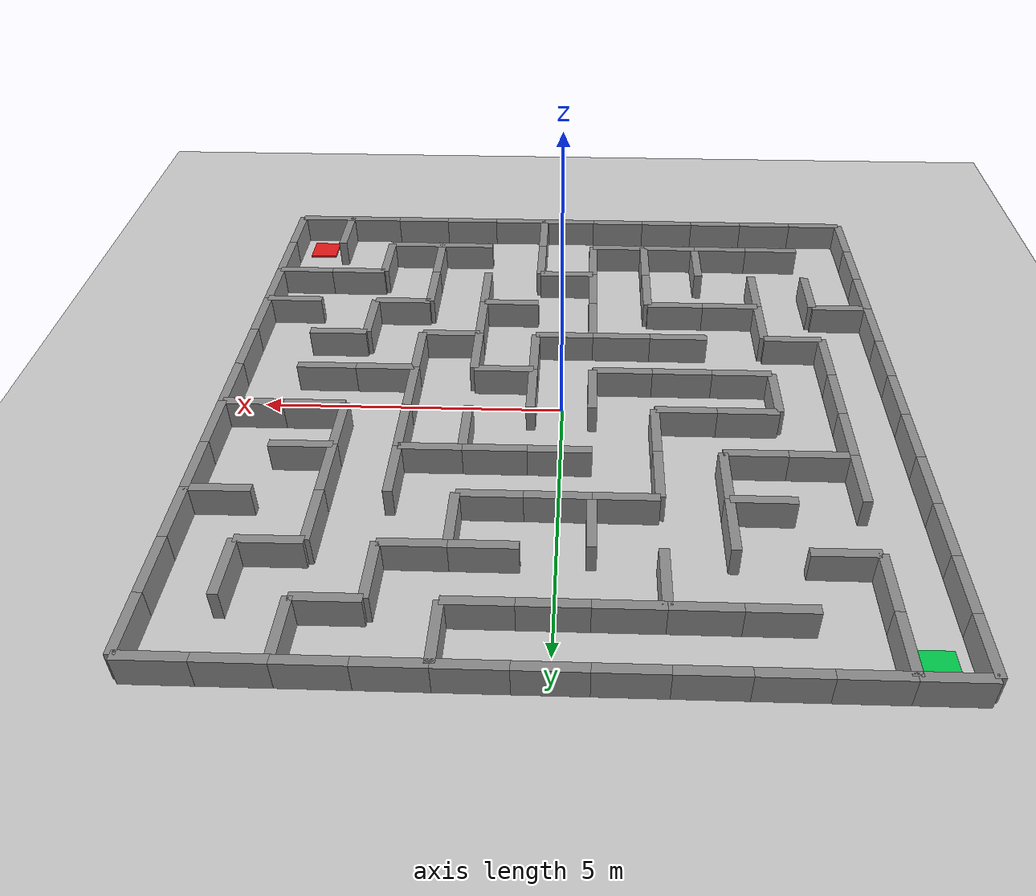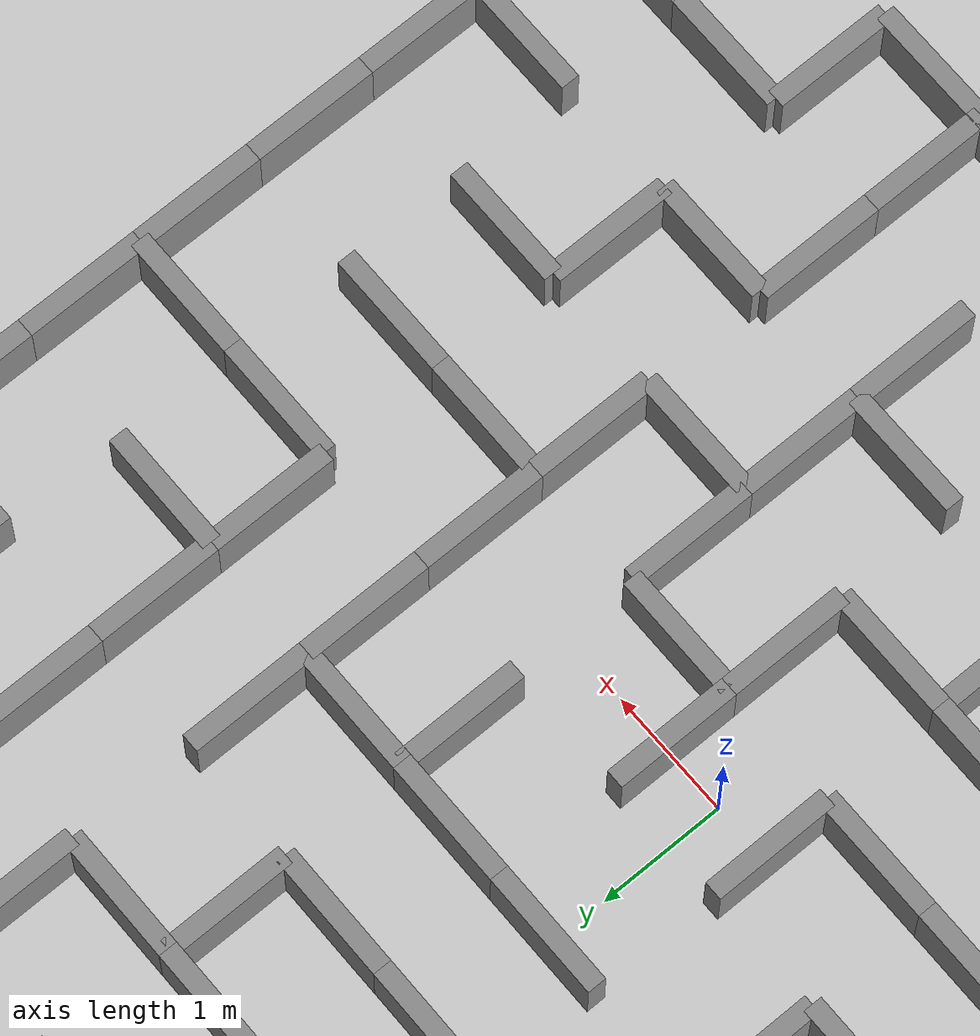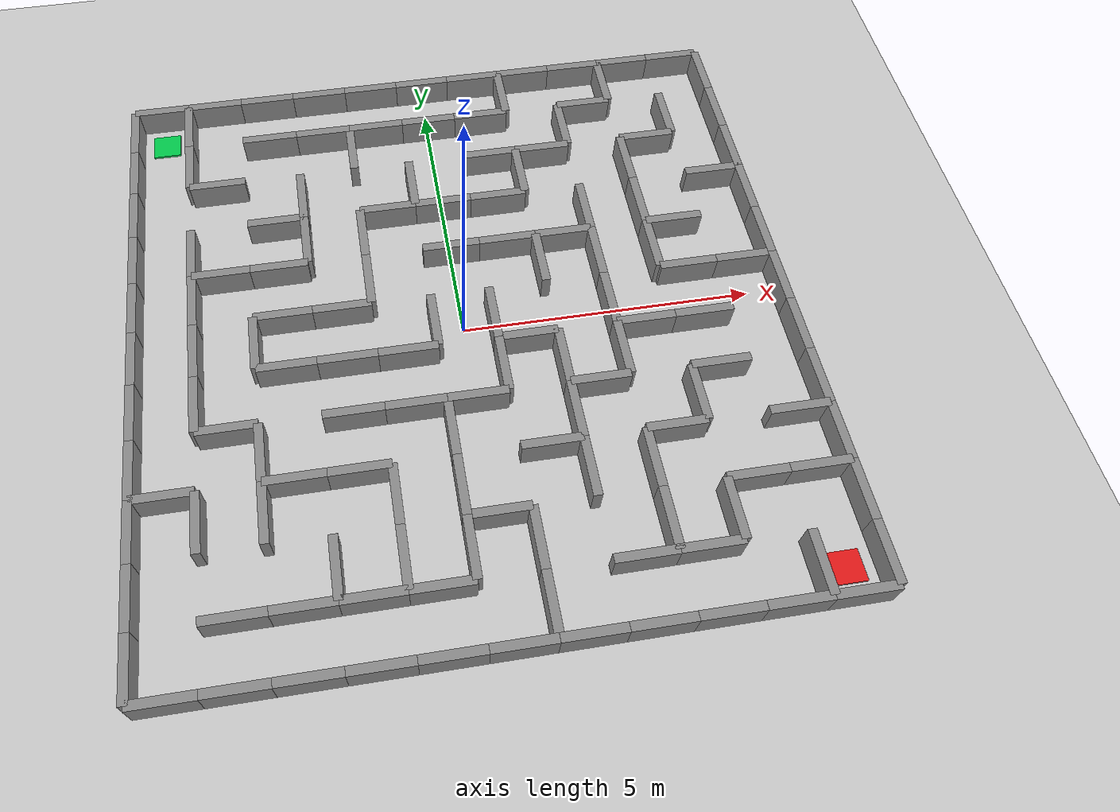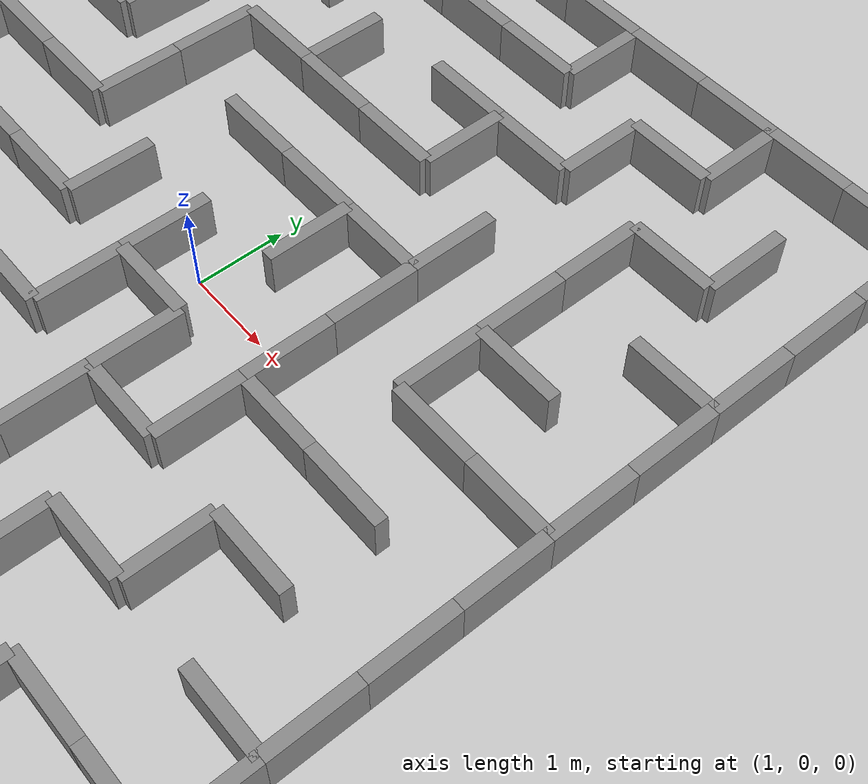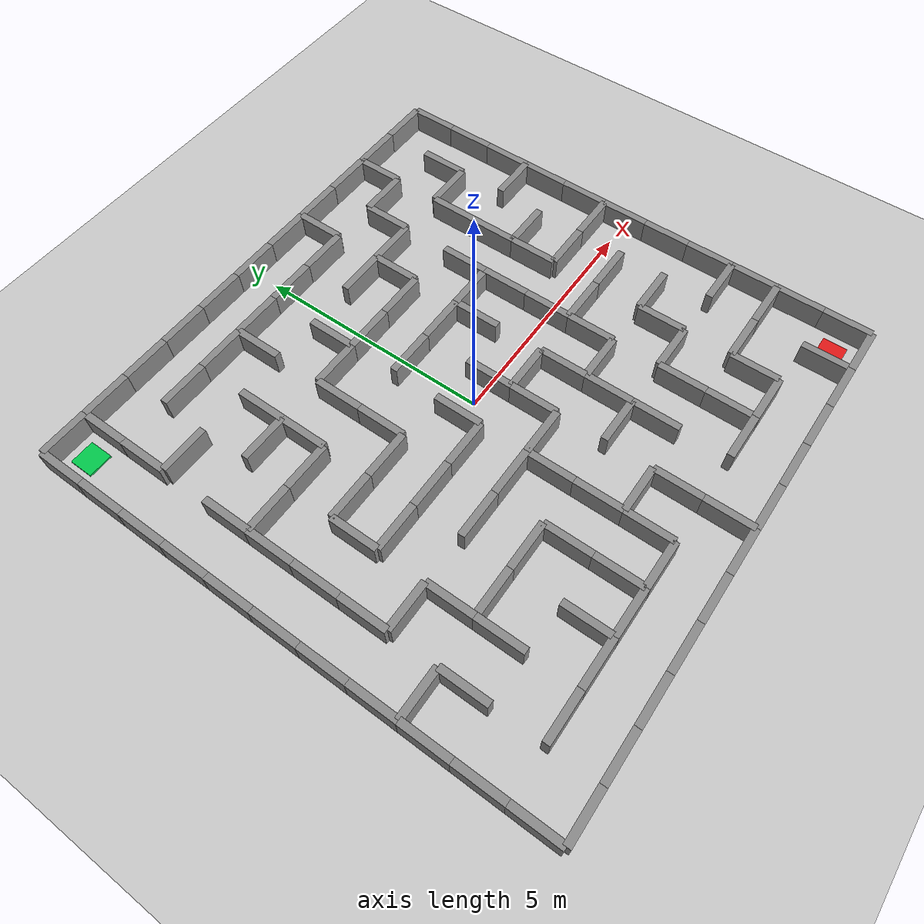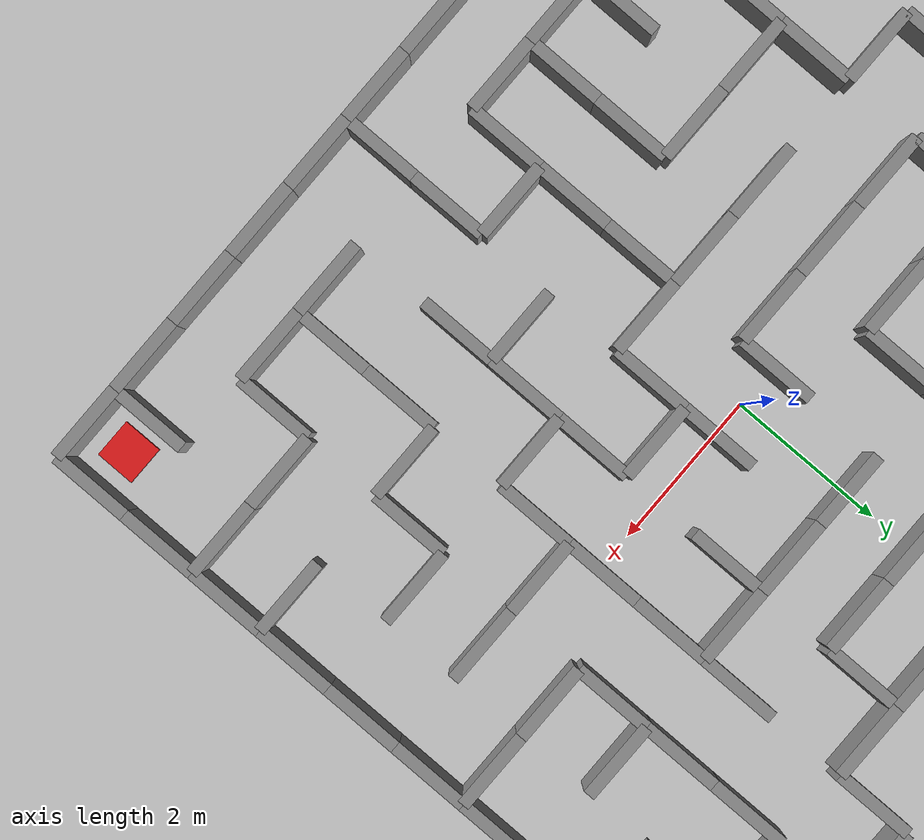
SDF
<?xml version="1.0" ?>
<sdf version="1.6">
  <world name="maze_world">

    <include><uri>model://ground_plane</uri></include>
    <include><uri>model://sun</uri></include>

    <physics type="ode">
      <real_time_update_rate>1000</real_time_update_rate>
      <max_step_size>0.001</max_step_size>
      <real_time_factor>1</real_time_factor>
      <ode>
        <solver>
          <type>quick</type>
          <iters>150</iters>
          <precon_iters>0</precon_iters>
          <sor>1.400000</sor>
        </solver>
        <constraints>
          <cfm>0.00001</cfm>
          <erp>0.2</erp>
          <contact_max_correcting_vel>2000</contact_max_correcting_vel>
          <contact_surface_layer>0.01</contact_surface_layer>
        </constraints>
      </ode>
    </physics>

    <scene>
      <ambient>0.4 0.4 0.4 1</ambient>
      <background>0.7 0.7 0.7 1</background>
      <shadows>true</shadows>
    </scene>

    <model name="hw_0_0">
      <static>true</static>
      <pose>-5.0000 5.5000 0.2500 0 0 0.0000</pose>
      <link name="link">
        <collision name="col">
          <geometry><box><size>1.0000 0.15 0.5</size></box></geometry>
          <surface>
            <friction><ode><mu>0.8</mu><mu2>0.8</mu2></ode></friction>
          </surface>
        </collision>
        <visual name="vis">
          <geometry><box><size>1.0000 0.15 0.5</size></box></geometry>
          <material>
            <ambient>0.55 0.55 0.55 1</ambient>
            <diffuse>0.55 0.55 0.55 1</diffuse>
          </material>
        </visual>
      </link>
    </model>
    <model name="hw_0_1">
      <static>true</static>
      <pose>-4.0000 5.5000 0.2500 0 0 0.0000</pose>
      <link name="link">
        <collision name="col">
          <geometry><box><size>1.0000 0.15 0.5</size></box></geometry>
          <surface>
            <friction><ode><mu>0.8</mu><mu2>0.8</mu2></ode></friction>
          </surface>
        </collision>
        <visual name="vis">
          <geometry><box><size>1.0000 0.15 0.5</size></box></geometry>
          <material>
            <ambient>0.55 0.55 0.55 1</ambient>
            <diffuse>0.55 0.55 0.55 1</diffuse>
          </material>
        </visual>
      </link>
    </model>
    <model name="hw_0_2">
      <static>true</static>
      <pose>-3.0000 5.5000 0.2500 0 0 0.0000</pose>
      <link name="link">
        <collision name="col">
          <geometry><box><size>1.0000 0.15 0.5</size></box></geometry>
          <surface>
            <friction><ode><mu>0.8</mu><mu2>0.8</mu2></ode></friction>
          </surface>
        </collision>
        <visual name="vis">
          <geometry><box><size>1.0000 0.15 0.5</size></box></geometry>
          <material>
            <ambient>0.55 0.55 0.55 1</ambient>
            <diffuse>0.55 0.55 0.55 1</diffuse>
          </material>
        </visual>
      </link>
    </model>
    <model name="hw_0_3">
      <static>true</static>
      <pose>-2.0000 5.5000 0.2500 0 0 0.0000</pose>
      <link name="link">
        <collision name="col">
          <geometry><box><size>1.0000 0.15 0.5</size></box></geometry>
          <surface>
            <friction><ode><mu>0.8</mu><mu2>0.8</mu2></ode></friction>
          </surface>
        </collision>
        <visual name="vis">
          <geometry><box><size>1.0000 0.15 0.5</size></box></geometry>
          <material>
            <ambient>0.55 0.55 0.55 1</ambient>
            <diffuse>0.55 0.55 0.55 1</diffuse>
          </material>
        </visual>
      </link>
    </model>
    <model name="hw_0_4">
      <static>true</static>
      <pose>-1.0000 5.5000 0.2500 0 0 0.0000</pose>
      <link name="link">
        <collision name="col">
          <geometry><box><size>1.0000 0.15 0.5</size></box></geometry>
          <surface>
            <friction><ode><mu>0.8</mu><mu2>0.8</mu2></ode></friction>
          </surface>
        </collision>
        <visual name="vis">
          <geometry><box><size>1.0000 0.15 0.5</size></box></geometry>
          <material>
            <ambient>0.55 0.55 0.55 1</ambient>
            <diffuse>0.55 0.55 0.55 1</diffuse>
          </material>
        </visual>
      </link>
    </model>
    <model name="hw_0_5">
      <static>true</static>
      <pose>0.0000 5.5000 0.2500 0 0 0.0000</pose>
      <link name="link">
        <collision name="col">
          <geometry><box><size>1.0000 0.15 0.5</size></box></geometry>
          <surface>
            <friction><ode><mu>0.8</mu><mu2>0.8</mu2></ode></friction>
          </surface>
        </collision>
        <visual name="vis">
          <geometry><box><size>1.0000 0.15 0.5</size></box></geometry>
          <material>
            <ambient>0.55 0.55 0.55 1</ambient>
            <diffuse>0.55 0.55 0.55 1</diffuse>
          </material>
        </visual>
      </link>
    </model>
    <model name="hw_0_6">
      <static>true</static>
      <pose>1.0000 5.5000 0.2500 0 0 0.0000</pose>
      <link name="link">
        <collision name="col">
          <geometry><box><size>1.0000 0.15 0.5</size></box></geometry>
          <surface>
            <friction><ode><mu>0.8</mu><mu2>0.8</mu2></ode></friction>
          </surface>
        </collision>
        <visual name="vis">
          <geometry><box><size>1.0000 0.15 0.5</size></box></geometry>
          <material>
            <ambient>0.55 0.55 0.55 1</ambient>
            <diffuse>0.55 0.55 0.55 1</diffuse>
          </material>
        </visual>
      </link>
    </model>
    <model name="hw_0_7">
      <static>true</static>
      <pose>2.0000 5.5000 0.2500 0 0 0.0000</pose>
      <link name="link">
        <collision name="col">
          <geometry><box><size>1.0000 0.15 0.5</size></box></geometry>
          <surface>
            <friction><ode><mu>0.8</mu><mu2>0.8</mu2></ode></friction>
          </surface>
        </collision>
        <visual name="vis">
          <geometry><box><size>1.0000 0.15 0.5</size></box></geometry>
          <material>
            <ambient>0.55 0.55 0.55 1</ambient>
            <diffuse>0.55 0.55 0.55 1</diffuse>
          </material>
        </visual>
      </link>
    </model>
    <model name="hw_0_8">
      <static>true</static>
      <pose>3.0000 5.5000 0.2500 0 0 0.0000</pose>
      <link name="link">
        <collision name="col">
          <geometry><box><size>1.0000 0.15 0.5</size></box></geometry>
          <surface>
            <friction><ode><mu>0.8</mu><mu2>0.8</mu2></ode></friction>
          </surface>
        </collision>
        <visual name="vis">
          <geometry><box><size>1.0000 0.15 0.5</size></box></geometry>
          <material>
            <ambient>0.55 0.55 0.55 1</ambient>
            <diffuse>0.55 0.55 0.55 1</diffuse>
          </material>
        </visual>
      </link>
    </model>
    <model name="hw_0_9">
      <static>true</static>
      <pose>4.0000 5.5000 0.2500 0 0 0.0000</pose>
      <link name="link">
        <collision name="col">
          <geometry><box><size>1.0000 0.15 0.5</size></box></geometry>
          <surface>
            <friction><ode><mu>0.8</mu><mu2>0.8</mu2></ode></friction>
          </surface>
        </collision>
        <visual name="vis">
          <geometry><box><size>1.0000 0.15 0.5</size></box></geometry>
          <material>
            <ambient>0.55 0.55 0.55 1</ambient>
            <diffuse>0.55 0.55 0.55 1</diffuse>
          </material>
        </visual>
      </link>
    </model>
    <model name="hw_0_10">
      <static>true</static>
      <pose>5.0000 5.5000 0.2500 0 0 0.0000</pose>
      <link name="link">
        <collision name="col">
          <geometry><box><size>1.0000 0.15 0.5</size></box></geometry>
          <surface>
            <friction><ode><mu>0.8</mu><mu2>0.8</mu2></ode></friction>
          </surface>
        </collision>
        <visual name="vis">
          <geometry><box><size>1.0000 0.15 0.5</size></box></geometry>
          <material>
            <ambient>0.55 0.55 0.55 1</ambient>
            <diffuse>0.55 0.55 0.55 1</diffuse>
          </material>
        </visual>
      </link>
    </model>
    <model name="hw_1_2">
      <static>true</static>
      <pose>-3.0000 4.5000 0.2500 0 0 0.0000</pose>
      <link name="link">
        <collision name="col">
          <geometry><box><size>1.0000 0.15 0.5</size></box></geometry>
          <surface>
            <friction><ode><mu>0.8</mu><mu2>0.8</mu2></ode></friction>
          </surface>
        </collision>
        <visual name="vis">
          <geometry><box><size>1.0000 0.15 0.5</size></box></geometry>
          <material>
            <ambient>0.55 0.55 0.55 1</ambient>
            <diffuse>0.55 0.55 0.55 1</diffuse>
          </material>
        </visual>
      </link>
    </model>
    <model name="hw_1_3">
      <static>true</static>
      <pose>-2.0000 4.5000 0.2500 0 0 0.0000</pose>
      <link name="link">
        <collision name="col">
          <geometry><box><size>1.0000 0.15 0.5</size></box></geometry>
          <surface>
            <friction><ode><mu>0.8</mu><mu2>0.8</mu2></ode></friction>
          </surface>
        </collision>
        <visual name="vis">
          <geometry><box><size>1.0000 0.15 0.5</size></box></geometry>
          <material>
            <ambient>0.55 0.55 0.55 1</ambient>
            <diffuse>0.55 0.55 0.55 1</diffuse>
          </material>
        </visual>
      </link>
    </model>
    <model name="hw_1_4">
      <static>true</static>
      <pose>-1.0000 4.5000 0.2500 0 0 0.0000</pose>
      <link name="link">
        <collision name="col">
          <geometry><box><size>1.0000 0.15 0.5</size></box></geometry>
          <surface>
            <friction><ode><mu>0.8</mu><mu2>0.8</mu2></ode></friction>
          </surface>
        </collision>
        <visual name="vis">
          <geometry><box><size>1.0000 0.15 0.5</size></box></geometry>
          <material>
            <ambient>0.55 0.55 0.55 1</ambient>
            <diffuse>0.55 0.55 0.55 1</diffuse>
          </material>
        </visual>
      </link>
    </model>
    <model name="hw_1_5">
      <static>true</static>
      <pose>0.0000 4.5000 0.2500 0 0 0.0000</pose>
      <link name="link">
        <collision name="col">
          <geometry><box><size>1.0000 0.15 0.5</size></box></geometry>
          <surface>
            <friction><ode><mu>0.8</mu><mu2>0.8</mu2></ode></friction>
          </surface>
        </collision>
        <visual name="vis">
          <geometry><box><size>1.0000 0.15 0.5</size></box></geometry>
          <material>
            <ambient>0.55 0.55 0.55 1</ambient>
            <diffuse>0.55 0.55 0.55 1</diffuse>
          </material>
        </visual>
      </link>
    </model>
    <model name="hw_1_6">
      <static>true</static>
      <pose>1.0000 4.5000 0.2500 0 0 0.0000</pose>
      <link name="link">
        <collision name="col">
          <geometry><box><size>1.0000 0.15 0.5</size></box></geometry>
          <surface>
            <friction><ode><mu>0.8</mu><mu2>0.8</mu2></ode></friction>
          </surface>
        </collision>
        <visual name="vis">
          <geometry><box><size>1.0000 0.15 0.5</size></box></geometry>
          <material>
            <ambient>0.55 0.55 0.55 1</ambient>
            <diffuse>0.55 0.55 0.55 1</diffuse>
          </material>
        </visual>
      </link>
    </model>
    <model name="hw_1_8">
      <static>true</static>
      <pose>3.0000 4.5000 0.2500 0 0 0.0000</pose>
      <link name="link">
        <collision name="col">
          <geometry><box><size>1.0000 0.15 0.5</size></box></geometry>
          <surface>
            <friction><ode><mu>0.8</mu><mu2>0.8</mu2></ode></friction>
          </surface>
        </collision>
        <visual name="vis">
          <geometry><box><size>1.0000 0.15 0.5</size></box></geometry>
          <material>
            <ambient>0.55 0.55 0.55 1</ambient>
            <diffuse>0.55 0.55 0.55 1</diffuse>
          </material>
        </visual>
      </link>
    </model>
    <model name="hw_2_1">
      <static>true</static>
      <pose>-4.0000 3.5000 0.2500 0 0 0.0000</pose>
      <link name="link">
        <collision name="col">
          <geometry><box><size>1.0000 0.15 0.5</size></box></geometry>
          <surface>
            <friction><ode><mu>0.8</mu><mu2>0.8</mu2></ode></friction>
          </surface>
        </collision>
        <visual name="vis">
          <geometry><box><size>1.0000 0.15 0.5</size></box></geometry>
          <material>
            <ambient>0.55 0.55 0.55 1</ambient>
            <diffuse>0.55 0.55 0.55 1</diffuse>
          </material>
        </visual>
      </link>
    </model>
    <model name="hw_2_6">
      <static>true</static>
      <pose>1.0000 3.5000 0.2500 0 0 0.0000</pose>
      <link name="link">
        <collision name="col">
          <geometry><box><size>1.0000 0.15 0.5</size></box></geometry>
          <surface>
            <friction><ode><mu>0.8</mu><mu2>0.8</mu2></ode></friction>
          </surface>
        </collision>
        <visual name="vis">
          <geometry><box><size>1.0000 0.15 0.5</size></box></geometry>
          <material>
            <ambient>0.55 0.55 0.55 1</ambient>
            <diffuse>0.55 0.55 0.55 1</diffuse>
          </material>
        </visual>
      </link>
    </model>
    <model name="hw_2_7">
      <static>true</static>
      <pose>2.0000 3.5000 0.2500 0 0 0.0000</pose>
      <link name="link">
        <collision name="col">
          <geometry><box><size>1.0000 0.15 0.5</size></box></geometry>
          <surface>
            <friction><ode><mu>0.8</mu><mu2>0.8</mu2></ode></friction>
          </surface>
        </collision>
        <visual name="vis">
          <geometry><box><size>1.0000 0.15 0.5</size></box></geometry>
          <material>
            <ambient>0.55 0.55 0.55 1</ambient>
            <diffuse>0.55 0.55 0.55 1</diffuse>
          </material>
        </visual>
      </link>
    </model>
    <model name="hw_2_9">
      <static>true</static>
      <pose>4.0000 3.5000 0.2500 0 0 0.0000</pose>
      <link name="link">
        <collision name="col">
          <geometry><box><size>1.0000 0.15 0.5</size></box></geometry>
          <surface>
            <friction><ode><mu>0.8</mu><mu2>0.8</mu2></ode></friction>
          </surface>
        </collision>
        <visual name="vis">
          <geometry><box><size>1.0000 0.15 0.5</size></box></geometry>
          <material>
            <ambient>0.55 0.55 0.55 1</ambient>
            <diffuse>0.55 0.55 0.55 1</diffuse>
          </material>
        </visual>
      </link>
    </model>
    <model name="hw_3_2">
      <static>true</static>
      <pose>-3.0000 2.5000 0.2500 0 0 0.0000</pose>
      <link name="link">
        <collision name="col">
          <geometry><box><size>1.0000 0.15 0.5</size></box></geometry>
          <surface>
            <friction><ode><mu>0.8</mu><mu2>0.8</mu2></ode></friction>
          </surface>
        </collision>
        <visual name="vis">
          <geometry><box><size>1.0000 0.15 0.5</size></box></geometry>
          <material>
            <ambient>0.55 0.55 0.55 1</ambient>
            <diffuse>0.55 0.55 0.55 1</diffuse>
          </material>
        </visual>
      </link>
    </model>
    <model name="hw_3_4">
      <static>true</static>
      <pose>-1.0000 2.5000 0.2500 0 0 0.0000</pose>
      <link name="link">
        <collision name="col">
          <geometry><box><size>1.0000 0.15 0.5</size></box></geometry>
          <surface>
            <friction><ode><mu>0.8</mu><mu2>0.8</mu2></ode></friction>
          </surface>
        </collision>
        <visual name="vis">
          <geometry><box><size>1.0000 0.15 0.5</size></box></geometry>
          <material>
            <ambient>0.55 0.55 0.55 1</ambient>
            <diffuse>0.55 0.55 0.55 1</diffuse>
          </material>
        </visual>
      </link>
    </model>
    <model name="hw_3_5">
      <static>true</static>
      <pose>0.0000 2.5000 0.2500 0 0 0.0000</pose>
      <link name="link">
        <collision name="col">
          <geometry><box><size>1.0000 0.15 0.5</size></box></geometry>
          <surface>
            <friction><ode><mu>0.8</mu><mu2>0.8</mu2></ode></friction>
          </surface>
        </collision>
        <visual name="vis">
          <geometry><box><size>1.0000 0.15 0.5</size></box></geometry>
          <material>
            <ambient>0.55 0.55 0.55 1</ambient>
            <diffuse>0.55 0.55 0.55 1</diffuse>
          </material>
        </visual>
      </link>
    </model>
    <model name="hw_3_6">
      <static>true</static>
      <pose>1.0000 2.5000 0.2500 0 0 0.0000</pose>
      <link name="link">
        <collision name="col">
          <geometry><box><size>1.0000 0.15 0.5</size></box></geometry>
          <surface>
            <friction><ode><mu>0.8</mu><mu2>0.8</mu2></ode></friction>
          </surface>
        </collision>
        <visual name="vis">
          <geometry><box><size>1.0000 0.15 0.5</size></box></geometry>
          <material>
            <ambient>0.55 0.55 0.55 1</ambient>
            <diffuse>0.55 0.55 0.55 1</diffuse>
          </material>
        </visual>
      </link>
    </model>
    <model name="hw_3_10">
      <static>true</static>
      <pose>5.0000 2.5000 0.2500 0 0 0.0000</pose>
      <link name="link">
        <collision name="col">
          <geometry><box><size>1.0000 0.15 0.5</size></box></geometry>
          <surface>
            <friction><ode><mu>0.8</mu><mu2>0.8</mu2></ode></friction>
          </surface>
        </collision>
        <visual name="vis">
          <geometry><box><size>1.0000 0.15 0.5</size></box></geometry>
          <material>
            <ambient>0.55 0.55 0.55 1</ambient>
            <diffuse>0.55 0.55 0.55 1</diffuse>
          </material>
        </visual>
      </link>
    </model>
    <model name="hw_4_1">
      <static>true</static>
      <pose>-4.0000 1.5000 0.2500 0 0 0.0000</pose>
      <link name="link">
        <collision name="col">
          <geometry><box><size>1.0000 0.15 0.5</size></box></geometry>
          <surface>
            <friction><ode><mu>0.8</mu><mu2>0.8</mu2></ode></friction>
          </surface>
        </collision>
        <visual name="vis">
          <geometry><box><size>1.0000 0.15 0.5</size></box></geometry>
          <material>
            <ambient>0.55 0.55 0.55 1</ambient>
            <diffuse>0.55 0.55 0.55 1</diffuse>
          </material>
        </visual>
      </link>
    </model>
    <model name="hw_4_2">
      <static>true</static>
      <pose>-3.0000 1.5000 0.2500 0 0 0.0000</pose>
      <link name="link">
        <collision name="col">
          <geometry><box><size>1.0000 0.15 0.5</size></box></geometry>
          <surface>
            <friction><ode><mu>0.8</mu><mu2>0.8</mu2></ode></friction>
          </surface>
        </collision>
        <visual name="vis">
          <geometry><box><size>1.0000 0.15 0.5</size></box></geometry>
          <material>
            <ambient>0.55 0.55 0.55 1</ambient>
            <diffuse>0.55 0.55 0.55 1</diffuse>
          </material>
        </visual>
      </link>
    </model>
    <model name="hw_4_5">
      <static>true</static>
      <pose>0.0000 1.5000 0.2500 0 0 0.0000</pose>
      <link name="link">
        <collision name="col">
          <geometry><box><size>1.0000 0.15 0.5</size></box></geometry>
          <surface>
            <friction><ode><mu>0.8</mu><mu2>0.8</mu2></ode></friction>
          </surface>
        </collision>
        <visual name="vis">
          <geometry><box><size>1.0000 0.15 0.5</size></box></geometry>
          <material>
            <ambient>0.55 0.55 0.55 1</ambient>
            <diffuse>0.55 0.55 0.55 1</diffuse>
          </material>
        </visual>
      </link>
    </model>
    <model name="hw_4_6">
      <static>true</static>
      <pose>1.0000 1.5000 0.2500 0 0 0.0000</pose>
      <link name="link">
        <collision name="col">
          <geometry><box><size>1.0000 0.15 0.5</size></box></geometry>
          <surface>
            <friction><ode><mu>0.8</mu><mu2>0.8</mu2></ode></friction>
          </surface>
        </collision>
        <visual name="vis">
          <geometry><box><size>1.0000 0.15 0.5</size></box></geometry>
          <material>
            <ambient>0.55 0.55 0.55 1</ambient>
            <diffuse>0.55 0.55 0.55 1</diffuse>
          </material>
        </visual>
      </link>
    </model>
    <model name="hw_4_7">
      <static>true</static>
      <pose>2.0000 1.5000 0.2500 0 0 0.0000</pose>
      <link name="link">
        <collision name="col">
          <geometry><box><size>1.0000 0.15 0.5</size></box></geometry>
          <surface>
            <friction><ode><mu>0.8</mu><mu2>0.8</mu2></ode></friction>
          </surface>
        </collision>
        <visual name="vis">
          <geometry><box><size>1.0000 0.15 0.5</size></box></geometry>
          <material>
            <ambient>0.55 0.55 0.55 1</ambient>
            <diffuse>0.55 0.55 0.55 1</diffuse>
          </material>
        </visual>
      </link>
    </model>
    <model name="hw_4_9">
      <static>true</static>
      <pose>4.0000 1.5000 0.2500 0 0 0.0000</pose>
      <link name="link">
        <collision name="col">
          <geometry><box><size>1.0000 0.15 0.5</size></box></geometry>
          <surface>
            <friction><ode><mu>0.8</mu><mu2>0.8</mu2></ode></friction>
          </surface>
        </collision>
        <visual name="vis">
          <geometry><box><size>1.0000 0.15 0.5</size></box></geometry>
          <material>
            <ambient>0.55 0.55 0.55 1</ambient>
            <diffuse>0.55 0.55 0.55 1</diffuse>
          </material>
        </visual>
      </link>
    </model>
    <model name="hw_5_2">
      <static>true</static>
      <pose>-3.0000 0.5000 0.2500 0 0 0.0000</pose>
      <link name="link">
        <collision name="col">
          <geometry><box><size>1.0000 0.15 0.5</size></box></geometry>
          <surface>
            <friction><ode><mu>0.8</mu><mu2>0.8</mu2></ode></friction>
          </surface>
        </collision>
        <visual name="vis">
          <geometry><box><size>1.0000 0.15 0.5</size></box></geometry>
          <material>
            <ambient>0.55 0.55 0.55 1</ambient>
            <diffuse>0.55 0.55 0.55 1</diffuse>
          </material>
        </visual>
      </link>
    </model>
    <model name="hw_5_3">
      <static>true</static>
      <pose>-2.0000 0.5000 0.2500 0 0 0.0000</pose>
      <link name="link">
        <collision name="col">
          <geometry><box><size>1.0000 0.15 0.5</size></box></geometry>
          <surface>
            <friction><ode><mu>0.8</mu><mu2>0.8</mu2></ode></friction>
          </surface>
        </collision>
        <visual name="vis">
          <geometry><box><size>1.0000 0.15 0.5</size></box></geometry>
          <material>
            <ambient>0.55 0.55 0.55 1</ambient>
            <diffuse>0.55 0.55 0.55 1</diffuse>
          </material>
        </visual>
      </link>
    </model>
    <model name="hw_5_9">
      <static>true</static>
      <pose>4.0000 0.5000 0.2500 0 0 0.0000</pose>
      <link name="link">
        <collision name="col">
          <geometry><box><size>1.0000 0.15 0.5</size></box></geometry>
          <surface>
            <friction><ode><mu>0.8</mu><mu2>0.8</mu2></ode></friction>
          </surface>
        </collision>
        <visual name="vis">
          <geometry><box><size>1.0000 0.15 0.5</size></box></geometry>
          <material>
            <ambient>0.55 0.55 0.55 1</ambient>
            <diffuse>0.55 0.55 0.55 1</diffuse>
          </material>
        </visual>
      </link>
    </model>
    <model name="hw_5_10">
      <static>true</static>
      <pose>5.0000 0.5000 0.2500 0 0 0.0000</pose>
      <link name="link">
        <collision name="col">
          <geometry><box><size>1.0000 0.15 0.5</size></box></geometry>
          <surface>
            <friction><ode><mu>0.8</mu><mu2>0.8</mu2></ode></friction>
          </surface>
        </collision>
        <visual name="vis">
          <geometry><box><size>1.0000 0.15 0.5</size></box></geometry>
          <material>
            <ambient>0.55 0.55 0.55 1</ambient>
            <diffuse>0.55 0.55 0.55 1</diffuse>
          </material>
        </visual>
      </link>
    </model>
    <model name="hw_6_2">
      <static>true</static>
      <pose>-3.0000 -0.5000 0.2500 0 0 0.0000</pose>
      <link name="link">
        <collision name="col">
          <geometry><box><size>1.0000 0.15 0.5</size></box></geometry>
          <surface>
            <friction><ode><mu>0.8</mu><mu2>0.8</mu2></ode></friction>
          </surface>
        </collision>
        <visual name="vis">
          <geometry><box><size>1.0000 0.15 0.5</size></box></geometry>
          <material>
            <ambient>0.55 0.55 0.55 1</ambient>
            <diffuse>0.55 0.55 0.55 1</diffuse>
          </material>
        </visual>
      </link>
    </model>
    <model name="hw_6_3">
      <static>true</static>
      <pose>-2.0000 -0.5000 0.2500 0 0 0.0000</pose>
      <link name="link">
        <collision name="col">
          <geometry><box><size>1.0000 0.15 0.5</size></box></geometry>
          <surface>
            <friction><ode><mu>0.8</mu><mu2>0.8</mu2></ode></friction>
          </surface>
        </collision>
        <visual name="vis">
          <geometry><box><size>1.0000 0.15 0.5</size></box></geometry>
          <material>
            <ambient>0.55 0.55 0.55 1</ambient>
            <diffuse>0.55 0.55 0.55 1</diffuse>
          </material>
        </visual>
      </link>
    </model>
    <model name="hw_6_4">
      <static>true</static>
      <pose>-1.0000 -0.5000 0.2500 0 0 0.0000</pose>
      <link name="link">
        <collision name="col">
          <geometry><box><size>1.0000 0.15 0.5</size></box></geometry>
          <surface>
            <friction><ode><mu>0.8</mu><mu2>0.8</mu2></ode></friction>
          </surface>
        </collision>
        <visual name="vis">
          <geometry><box><size>1.0000 0.15 0.5</size></box></geometry>
          <material>
            <ambient>0.55 0.55 0.55 1</ambient>
            <diffuse>0.55 0.55 0.55 1</diffuse>
          </material>
        </visual>
      </link>
    </model>
    <model name="hw_6_6">
      <static>true</static>
      <pose>1.0000 -0.5000 0.2500 0 0 0.0000</pose>
      <link name="link">
        <collision name="col">
          <geometry><box><size>1.0000 0.15 0.5</size></box></geometry>
          <surface>
            <friction><ode><mu>0.8</mu><mu2>0.8</mu2></ode></friction>
          </surface>
        </collision>
        <visual name="vis">
          <geometry><box><size>1.0000 0.15 0.5</size></box></geometry>
          <material>
            <ambient>0.55 0.55 0.55 1</ambient>
            <diffuse>0.55 0.55 0.55 1</diffuse>
          </material>
        </visual>
      </link>
    </model>
    <model name="hw_6_8">
      <static>true</static>
      <pose>3.0000 -0.5000 0.2500 0 0 0.0000</pose>
      <link name="link">
        <collision name="col">
          <geometry><box><size>1.0000 0.15 0.5</size></box></geometry>
          <surface>
            <friction><ode><mu>0.8</mu><mu2>0.8</mu2></ode></friction>
          </surface>
        </collision>
        <visual name="vis">
          <geometry><box><size>1.0000 0.15 0.5</size></box></geometry>
          <material>
            <ambient>0.55 0.55 0.55 1</ambient>
            <diffuse>0.55 0.55 0.55 1</diffuse>
          </material>
        </visual>
      </link>
    </model>
    <model name="hw_6_9">
      <static>true</static>
      <pose>4.0000 -0.5000 0.2500 0 0 0.0000</pose>
      <link name="link">
        <collision name="col">
          <geometry><box><size>1.0000 0.15 0.5</size></box></geometry>
          <surface>
            <friction><ode><mu>0.8</mu><mu2>0.8</mu2></ode></friction>
          </surface>
        </collision>
        <visual name="vis">
          <geometry><box><size>1.0000 0.15 0.5</size></box></geometry>
          <material>
            <ambient>0.55 0.55 0.55 1</ambient>
            <diffuse>0.55 0.55 0.55 1</diffuse>
          </material>
        </visual>
      </link>
    </model>
    <model name="hw_7_1">
      <static>true</static>
      <pose>-4.0000 -1.5000 0.2500 0 0 0.0000</pose>
      <link name="link">
        <collision name="col">
          <geometry><box><size>1.0000 0.15 0.5</size></box></geometry>
          <surface>
            <friction><ode><mu>0.8</mu><mu2>0.8</mu2></ode></friction>
          </surface>
        </collision>
        <visual name="vis">
          <geometry><box><size>1.0000 0.15 0.5</size></box></geometry>
          <material>
            <ambient>0.55 0.55 0.55 1</ambient>
            <diffuse>0.55 0.55 0.55 1</diffuse>
          </material>
        </visual>
      </link>
    </model>
    <model name="hw_7_3">
      <static>true</static>
      <pose>-2.0000 -1.5000 0.2500 0 0 0.0000</pose>
      <link name="link">
        <collision name="col">
          <geometry><box><size>1.0000 0.15 0.5</size></box></geometry>
          <surface>
            <friction><ode><mu>0.8</mu><mu2>0.8</mu2></ode></friction>
          </surface>
        </collision>
        <visual name="vis">
          <geometry><box><size>1.0000 0.15 0.5</size></box></geometry>
          <material>
            <ambient>0.55 0.55 0.55 1</ambient>
            <diffuse>0.55 0.55 0.55 1</diffuse>
          </material>
        </visual>
      </link>
    </model>
    <model name="hw_7_4">
      <static>true</static>
      <pose>-1.0000 -1.5000 0.2500 0 0 0.0000</pose>
      <link name="link">
        <collision name="col">
          <geometry><box><size>1.0000 0.15 0.5</size></box></geometry>
          <surface>
            <friction><ode><mu>0.8</mu><mu2>0.8</mu2></ode></friction>
          </surface>
        </collision>
        <visual name="vis">
          <geometry><box><size>1.0000 0.15 0.5</size></box></geometry>
          <material>
            <ambient>0.55 0.55 0.55 1</ambient>
            <diffuse>0.55 0.55 0.55 1</diffuse>
          </material>
        </visual>
      </link>
    </model>
    <model name="hw_7_5">
      <static>true</static>
      <pose>0.0000 -1.5000 0.2500 0 0 0.0000</pose>
      <link name="link">
        <collision name="col">
          <geometry><box><size>1.0000 0.15 0.5</size></box></geometry>
          <surface>
            <friction><ode><mu>0.8</mu><mu2>0.8</mu2></ode></friction>
          </surface>
        </collision>
        <visual name="vis">
          <geometry><box><size>1.0000 0.15 0.5</size></box></geometry>
          <material>
            <ambient>0.55 0.55 0.55 1</ambient>
            <diffuse>0.55 0.55 0.55 1</diffuse>
          </material>
        </visual>
      </link>
    </model>
    <model name="hw_7_7">
      <static>true</static>
      <pose>2.0000 -1.5000 0.2500 0 0 0.0000</pose>
      <link name="link">
        <collision name="col">
          <geometry><box><size>1.0000 0.15 0.5</size></box></geometry>
          <surface>
            <friction><ode><mu>0.8</mu><mu2>0.8</mu2></ode></friction>
          </surface>
        </collision>
        <visual name="vis">
          <geometry><box><size>1.0000 0.15 0.5</size></box></geometry>
          <material>
            <ambient>0.55 0.55 0.55 1</ambient>
            <diffuse>0.55 0.55 0.55 1</diffuse>
          </material>
        </visual>
      </link>
    </model>
    <model name="hw_7_9">
      <static>true</static>
      <pose>4.0000 -1.5000 0.2500 0 0 0.0000</pose>
      <link name="link">
        <collision name="col">
          <geometry><box><size>1.0000 0.15 0.5</size></box></geometry>
          <surface>
            <friction><ode><mu>0.8</mu><mu2>0.8</mu2></ode></friction>
          </surface>
        </collision>
        <visual name="vis">
          <geometry><box><size>1.0000 0.15 0.5</size></box></geometry>
          <material>
            <ambient>0.55 0.55 0.55 1</ambient>
            <diffuse>0.55 0.55 0.55 1</diffuse>
          </material>
        </visual>
      </link>
    </model>
    <model name="hw_8_0">
      <static>true</static>
      <pose>-5.0000 -2.5000 0.2500 0 0 0.0000</pose>
      <link name="link">
        <collision name="col">
          <geometry><box><size>1.0000 0.15 0.5</size></box></geometry>
          <surface>
            <friction><ode><mu>0.8</mu><mu2>0.8</mu2></ode></friction>
          </surface>
        </collision>
        <visual name="vis">
          <geometry><box><size>1.0000 0.15 0.5</size></box></geometry>
          <material>
            <ambient>0.55 0.55 0.55 1</ambient>
            <diffuse>0.55 0.55 0.55 1</diffuse>
          </material>
        </visual>
      </link>
    </model>
    <model name="hw_8_2">
      <static>true</static>
      <pose>-3.0000 -2.5000 0.2500 0 0 0.0000</pose>
      <link name="link">
        <collision name="col">
          <geometry><box><size>1.0000 0.15 0.5</size></box></geometry>
          <surface>
            <friction><ode><mu>0.8</mu><mu2>0.8</mu2></ode></friction>
          </surface>
        </collision>
        <visual name="vis">
          <geometry><box><size>1.0000 0.15 0.5</size></box></geometry>
          <material>
            <ambient>0.55 0.55 0.55 1</ambient>
            <diffuse>0.55 0.55 0.55 1</diffuse>
          </material>
        </visual>
      </link>
    </model>
    <model name="hw_8_3">
      <static>true</static>
      <pose>-2.0000 -2.5000 0.2500 0 0 0.0000</pose>
      <link name="link">
        <collision name="col">
          <geometry><box><size>1.0000 0.15 0.5</size></box></geometry>
          <surface>
            <friction><ode><mu>0.8</mu><mu2>0.8</mu2></ode></friction>
          </surface>
        </collision>
        <visual name="vis">
          <geometry><box><size>1.0000 0.15 0.5</size></box></geometry>
          <material>
            <ambient>0.55 0.55 0.55 1</ambient>
            <diffuse>0.55 0.55 0.55 1</diffuse>
          </material>
        </visual>
      </link>
    </model>
    <model name="hw_8_6">
      <static>true</static>
      <pose>1.0000 -2.5000 0.2500 0 0 0.0000</pose>
      <link name="link">
        <collision name="col">
          <geometry><box><size>1.0000 0.15 0.5</size></box></geometry>
          <surface>
            <friction><ode><mu>0.8</mu><mu2>0.8</mu2></ode></friction>
          </surface>
        </collision>
        <visual name="vis">
          <geometry><box><size>1.0000 0.15 0.5</size></box></geometry>
          <material>
            <ambient>0.55 0.55 0.55 1</ambient>
            <diffuse>0.55 0.55 0.55 1</diffuse>
          </material>
        </visual>
      </link>
    </model>
    <model name="hw_8_8">
      <static>true</static>
      <pose>3.0000 -2.5000 0.2500 0 0 0.0000</pose>
      <link name="link">
        <collision name="col">
          <geometry><box><size>1.0000 0.15 0.5</size></box></geometry>
          <surface>
            <friction><ode><mu>0.8</mu><mu2>0.8</mu2></ode></friction>
          </surface>
        </collision>
        <visual name="vis">
          <geometry><box><size>1.0000 0.15 0.5</size></box></geometry>
          <material>
            <ambient>0.55 0.55 0.55 1</ambient>
            <diffuse>0.55 0.55 0.55 1</diffuse>
          </material>
        </visual>
      </link>
    </model>
    <model name="hw_8_10">
      <static>true</static>
      <pose>5.0000 -2.5000 0.2500 0 0 0.0000</pose>
      <link name="link">
        <collision name="col">
          <geometry><box><size>1.0000 0.15 0.5</size></box></geometry>
          <surface>
            <friction><ode><mu>0.8</mu><mu2>0.8</mu2></ode></friction>
          </surface>
        </collision>
        <visual name="vis">
          <geometry><box><size>1.0000 0.15 0.5</size></box></geometry>
          <material>
            <ambient>0.55 0.55 0.55 1</ambient>
            <diffuse>0.55 0.55 0.55 1</diffuse>
          </material>
        </visual>
      </link>
    </model>
    <model name="hw_9_5">
      <static>true</static>
      <pose>0.0000 -3.5000 0.2500 0 0 0.0000</pose>
      <link name="link">
        <collision name="col">
          <geometry><box><size>1.0000 0.15 0.5</size></box></geometry>
          <surface>
            <friction><ode><mu>0.8</mu><mu2>0.8</mu2></ode></friction>
          </surface>
        </collision>
        <visual name="vis">
          <geometry><box><size>1.0000 0.15 0.5</size></box></geometry>
          <material>
            <ambient>0.55 0.55 0.55 1</ambient>
            <diffuse>0.55 0.55 0.55 1</diffuse>
          </material>
        </visual>
      </link>
    </model>
    <model name="hw_9_9">
      <static>true</static>
      <pose>4.0000 -3.5000 0.2500 0 0 0.0000</pose>
      <link name="link">
        <collision name="col">
          <geometry><box><size>1.0000 0.15 0.5</size></box></geometry>
          <surface>
            <friction><ode><mu>0.8</mu><mu2>0.8</mu2></ode></friction>
          </surface>
        </collision>
        <visual name="vis">
          <geometry><box><size>1.0000 0.15 0.5</size></box></geometry>
          <material>
            <ambient>0.55 0.55 0.55 1</ambient>
            <diffuse>0.55 0.55 0.55 1</diffuse>
          </material>
        </visual>
      </link>
    </model>
    <model name="hw_9_10">
      <static>true</static>
      <pose>5.0000 -3.5000 0.2500 0 0 0.0000</pose>
      <link name="link">
        <collision name="col">
          <geometry><box><size>1.0000 0.15 0.5</size></box></geometry>
          <surface>
            <friction><ode><mu>0.8</mu><mu2>0.8</mu2></ode></friction>
          </surface>
        </collision>
        <visual name="vis">
          <geometry><box><size>1.0000 0.15 0.5</size></box></geometry>
          <material>
            <ambient>0.55 0.55 0.55 1</ambient>
            <diffuse>0.55 0.55 0.55 1</diffuse>
          </material>
        </visual>
      </link>
    </model>
    <model name="hw_10_1">
      <static>true</static>
      <pose>-4.0000 -4.5000 0.2500 0 0 0.0000</pose>
      <link name="link">
        <collision name="col">
          <geometry><box><size>1.0000 0.15 0.5</size></box></geometry>
          <surface>
            <friction><ode><mu>0.8</mu><mu2>0.8</mu2></ode></friction>
          </surface>
        </collision>
        <visual name="vis">
          <geometry><box><size>1.0000 0.15 0.5</size></box></geometry>
          <material>
            <ambient>0.55 0.55 0.55 1</ambient>
            <diffuse>0.55 0.55 0.55 1</diffuse>
          </material>
        </visual>
      </link>
    </model>
    <model name="hw_10_2">
      <static>true</static>
      <pose>-3.0000 -4.5000 0.2500 0 0 0.0000</pose>
      <link name="link">
        <collision name="col">
          <geometry><box><size>1.0000 0.15 0.5</size></box></geometry>
          <surface>
            <friction><ode><mu>0.8</mu><mu2>0.8</mu2></ode></friction>
          </surface>
        </collision>
        <visual name="vis">
          <geometry><box><size>1.0000 0.15 0.5</size></box></geometry>
          <material>
            <ambient>0.55 0.55 0.55 1</ambient>
            <diffuse>0.55 0.55 0.55 1</diffuse>
          </material>
        </visual>
      </link>
    </model>
    <model name="hw_10_3">
      <static>true</static>
      <pose>-2.0000 -4.5000 0.2500 0 0 0.0000</pose>
      <link name="link">
        <collision name="col">
          <geometry><box><size>1.0000 0.15 0.5</size></box></geometry>
          <surface>
            <friction><ode><mu>0.8</mu><mu2>0.8</mu2></ode></friction>
          </surface>
        </collision>
        <visual name="vis">
          <geometry><box><size>1.0000 0.15 0.5</size></box></geometry>
          <material>
            <ambient>0.55 0.55 0.55 1</ambient>
            <diffuse>0.55 0.55 0.55 1</diffuse>
          </material>
        </visual>
      </link>
    </model>
    <model name="hw_10_4">
      <static>true</static>
      <pose>-1.0000 -4.5000 0.2500 0 0 0.0000</pose>
      <link name="link">
        <collision name="col">
          <geometry><box><size>1.0000 0.15 0.5</size></box></geometry>
          <surface>
            <friction><ode><mu>0.8</mu><mu2>0.8</mu2></ode></friction>
          </surface>
        </collision>
        <visual name="vis">
          <geometry><box><size>1.0000 0.15 0.5</size></box></geometry>
          <material>
            <ambient>0.55 0.55 0.55 1</ambient>
            <diffuse>0.55 0.55 0.55 1</diffuse>
          </material>
        </visual>
      </link>
    </model>
    <model name="hw_10_7">
      <static>true</static>
      <pose>2.0000 -4.5000 0.2500 0 0 0.0000</pose>
      <link name="link">
        <collision name="col">
          <geometry><box><size>1.0000 0.15 0.5</size></box></geometry>
          <surface>
            <friction><ode><mu>0.8</mu><mu2>0.8</mu2></ode></friction>
          </surface>
        </collision>
        <visual name="vis">
          <geometry><box><size>1.0000 0.15 0.5</size></box></geometry>
          <material>
            <ambient>0.55 0.55 0.55 1</ambient>
            <diffuse>0.55 0.55 0.55 1</diffuse>
          </material>
        </visual>
      </link>
    </model>
    <model name="hw_10_8">
      <static>true</static>
      <pose>3.0000 -4.5000 0.2500 0 0 0.0000</pose>
      <link name="link">
        <collision name="col">
          <geometry><box><size>1.0000 0.15 0.5</size></box></geometry>
          <surface>
            <friction><ode><mu>0.8</mu><mu2>0.8</mu2></ode></friction>
          </surface>
        </collision>
        <visual name="vis">
          <geometry><box><size>1.0000 0.15 0.5</size></box></geometry>
          <material>
            <ambient>0.55 0.55 0.55 1</ambient>
            <diffuse>0.55 0.55 0.55 1</diffuse>
          </material>
        </visual>
      </link>
    </model>
    <model name="hw_11_0">
      <static>true</static>
      <pose>-5.0000 -5.5000 0.2500 0 0 0.0000</pose>
      <link name="link">
        <collision name="col">
          <geometry><box><size>1.0000 0.15 0.5</size></box></geometry>
          <surface>
            <friction><ode><mu>0.8</mu><mu2>0.8</mu2></ode></friction>
          </surface>
        </collision>
        <visual name="vis">
          <geometry><box><size>1.0000 0.15 0.5</size></box></geometry>
          <material>
            <ambient>0.55 0.55 0.55 1</ambient>
            <diffuse>0.55 0.55 0.55 1</diffuse>
          </material>
        </visual>
      </link>
    </model>
    <model name="hw_11_1">
      <static>true</static>
      <pose>-4.0000 -5.5000 0.2500 0 0 0.0000</pose>
      <link name="link">
        <collision name="col">
          <geometry><box><size>1.0000 0.15 0.5</size></box></geometry>
          <surface>
            <friction><ode><mu>0.8</mu><mu2>0.8</mu2></ode></friction>
          </surface>
        </collision>
        <visual name="vis">
          <geometry><box><size>1.0000 0.15 0.5</size></box></geometry>
          <material>
            <ambient>0.55 0.55 0.55 1</ambient>
            <diffuse>0.55 0.55 0.55 1</diffuse>
          </material>
        </visual>
      </link>
    </model>
    <model name="hw_11_2">
      <static>true</static>
      <pose>-3.0000 -5.5000 0.2500 0 0 0.0000</pose>
      <link name="link">
        <collision name="col">
          <geometry><box><size>1.0000 0.15 0.5</size></box></geometry>
          <surface>
            <friction><ode><mu>0.8</mu><mu2>0.8</mu2></ode></friction>
          </surface>
        </collision>
        <visual name="vis">
          <geometry><box><size>1.0000 0.15 0.5</size></box></geometry>
          <material>
            <ambient>0.55 0.55 0.55 1</ambient>
            <diffuse>0.55 0.55 0.55 1</diffuse>
          </material>
        </visual>
      </link>
    </model>
    <model name="hw_11_3">
      <static>true</static>
      <pose>-2.0000 -5.5000 0.2500 0 0 0.0000</pose>
      <link name="link">
        <collision name="col">
          <geometry><box><size>1.0000 0.15 0.5</size></box></geometry>
          <surface>
            <friction><ode><mu>0.8</mu><mu2>0.8</mu2></ode></friction>
          </surface>
        </collision>
        <visual name="vis">
          <geometry><box><size>1.0000 0.15 0.5</size></box></geometry>
          <material>
            <ambient>0.55 0.55 0.55 1</ambient>
            <diffuse>0.55 0.55 0.55 1</diffuse>
          </material>
        </visual>
      </link>
    </model>
    <model name="hw_11_4">
      <static>true</static>
      <pose>-1.0000 -5.5000 0.2500 0 0 0.0000</pose>
      <link name="link">
        <collision name="col">
          <geometry><box><size>1.0000 0.15 0.5</size></box></geometry>
          <surface>
            <friction><ode><mu>0.8</mu><mu2>0.8</mu2></ode></friction>
          </surface>
        </collision>
        <visual name="vis">
          <geometry><box><size>1.0000 0.15 0.5</size></box></geometry>
          <material>
            <ambient>0.55 0.55 0.55 1</ambient>
            <diffuse>0.55 0.55 0.55 1</diffuse>
          </material>
        </visual>
      </link>
    </model>
    <model name="hw_11_5">
      <static>true</static>
      <pose>0.0000 -5.5000 0.2500 0 0 0.0000</pose>
      <link name="link">
        <collision name="col">
          <geometry><box><size>1.0000 0.15 0.5</size></box></geometry>
          <surface>
            <friction><ode><mu>0.8</mu><mu2>0.8</mu2></ode></friction>
          </surface>
        </collision>
        <visual name="vis">
          <geometry><box><size>1.0000 0.15 0.5</size></box></geometry>
          <material>
            <ambient>0.55 0.55 0.55 1</ambient>
            <diffuse>0.55 0.55 0.55 1</diffuse>
          </material>
        </visual>
      </link>
    </model>
    <model name="hw_11_6">
      <static>true</static>
      <pose>1.0000 -5.5000 0.2500 0 0 0.0000</pose>
      <link name="link">
        <collision name="col">
          <geometry><box><size>1.0000 0.15 0.5</size></box></geometry>
          <surface>
            <friction><ode><mu>0.8</mu><mu2>0.8</mu2></ode></friction>
          </surface>
        </collision>
        <visual name="vis">
          <geometry><box><size>1.0000 0.15 0.5</size></box></geometry>
          <material>
            <ambient>0.55 0.55 0.55 1</ambient>
            <diffuse>0.55 0.55 0.55 1</diffuse>
          </material>
        </visual>
      </link>
    </model>
    <model name="hw_11_7">
      <static>true</static>
      <pose>2.0000 -5.5000 0.2500 0 0 0.0000</pose>
      <link name="link">
        <collision name="col">
          <geometry><box><size>1.0000 0.15 0.5</size></box></geometry>
          <surface>
            <friction><ode><mu>0.8</mu><mu2>0.8</mu2></ode></friction>
          </surface>
        </collision>
        <visual name="vis">
          <geometry><box><size>1.0000 0.15 0.5</size></box></geometry>
          <material>
            <ambient>0.55 0.55 0.55 1</ambient>
            <diffuse>0.55 0.55 0.55 1</diffuse>
          </material>
        </visual>
      </link>
    </model>
    <model name="hw_11_8">
      <static>true</static>
      <pose>3.0000 -5.5000 0.2500 0 0 0.0000</pose>
      <link name="link">
        <collision name="col">
          <geometry><box><size>1.0000 0.15 0.5</size></box></geometry>
          <surface>
            <friction><ode><mu>0.8</mu><mu2>0.8</mu2></ode></friction>
          </surface>
        </collision>
        <visual name="vis">
          <geometry><box><size>1.0000 0.15 0.5</size></box></geometry>
          <material>
            <ambient>0.55 0.55 0.55 1</ambient>
            <diffuse>0.55 0.55 0.55 1</diffuse>
          </material>
        </visual>
      </link>
    </model>
    <model name="hw_11_9">
      <static>true</static>
      <pose>4.0000 -5.5000 0.2500 0 0 0.0000</pose>
      <link name="link">
        <collision name="col">
          <geometry><box><size>1.0000 0.15 0.5</size></box></geometry>
          <surface>
            <friction><ode><mu>0.8</mu><mu2>0.8</mu2></ode></friction>
          </surface>
        </collision>
        <visual name="vis">
          <geometry><box><size>1.0000 0.15 0.5</size></box></geometry>
          <material>
            <ambient>0.55 0.55 0.55 1</ambient>
            <diffuse>0.55 0.55 0.55 1</diffuse>
          </material>
        </visual>
      </link>
    </model>
    <model name="hw_11_10">
      <static>true</static>
      <pose>5.0000 -5.5000 0.2500 0 0 0.0000</pose>
      <link name="link">
        <collision name="col">
          <geometry><box><size>1.0000 0.15 0.5</size></box></geometry>
          <surface>
            <friction><ode><mu>0.8</mu><mu2>0.8</mu2></ode></friction>
          </surface>
        </collision>
        <visual name="vis">
          <geometry><box><size>1.0000 0.15 0.5</size></box></geometry>
          <material>
            <ambient>0.55 0.55 0.55 1</ambient>
            <diffuse>0.55 0.55 0.55 1</diffuse>
          </material>
        </visual>
      </link>
    </model>
    <model name="vw_0_0">
      <static>true</static>
      <pose>-5.5000 5.0000 0.2500 0 0 1.5708</pose>
      <link name="link">
        <collision name="col">
          <geometry><box><size>1.0000 0.15 0.5</size></box></geometry>
          <surface>
            <friction><ode><mu>0.8</mu><mu2>0.8</mu2></ode></friction>
          </surface>
        </collision>
        <visual name="vis">
          <geometry><box><size>1.0000 0.15 0.5</size></box></geometry>
          <material>
            <ambient>0.55 0.55 0.55 1</ambient>
            <diffuse>0.55 0.55 0.55 1</diffuse>
          </material>
        </visual>
      </link>
    </model>
    <model name="vw_0_1">
      <static>true</static>
      <pose>-5.5000 4.0000 0.2500 0 0 1.5708</pose>
      <link name="link">
        <collision name="col">
          <geometry><box><size>1.0000 0.15 0.5</size></box></geometry>
          <surface>
            <friction><ode><mu>0.8</mu><mu2>0.8</mu2></ode></friction>
          </surface>
        </collision>
        <visual name="vis">
          <geometry><box><size>1.0000 0.15 0.5</size></box></geometry>
          <material>
            <ambient>0.55 0.55 0.55 1</ambient>
            <diffuse>0.55 0.55 0.55 1</diffuse>
          </material>
        </visual>
      </link>
    </model>
    <model name="vw_0_2">
      <static>true</static>
      <pose>-5.5000 3.0000 0.2500 0 0 1.5708</pose>
      <link name="link">
        <collision name="col">
          <geometry><box><size>1.0000 0.15 0.5</size></box></geometry>
          <surface>
            <friction><ode><mu>0.8</mu><mu2>0.8</mu2></ode></friction>
          </surface>
        </collision>
        <visual name="vis">
          <geometry><box><size>1.0000 0.15 0.5</size></box></geometry>
          <material>
            <ambient>0.55 0.55 0.55 1</ambient>
            <diffuse>0.55 0.55 0.55 1</diffuse>
          </material>
        </visual>
      </link>
    </model>
    <model name="vw_0_3">
      <static>true</static>
      <pose>-5.5000 2.0000 0.2500 0 0 1.5708</pose>
      <link name="link">
        <collision name="col">
          <geometry><box><size>1.0000 0.15 0.5</size></box></geometry>
          <surface>
            <friction><ode><mu>0.8</mu><mu2>0.8</mu2></ode></friction>
          </surface>
        </collision>
        <visual name="vis">
          <geometry><box><size>1.0000 0.15 0.5</size></box></geometry>
          <material>
            <ambient>0.55 0.55 0.55 1</ambient>
            <diffuse>0.55 0.55 0.55 1</diffuse>
          </material>
        </visual>
      </link>
    </model>
    <model name="vw_0_4">
      <static>true</static>
      <pose>-5.5000 1.0000 0.2500 0 0 1.5708</pose>
      <link name="link">
        <collision name="col">
          <geometry><box><size>1.0000 0.15 0.5</size></box></geometry>
          <surface>
            <friction><ode><mu>0.8</mu><mu2>0.8</mu2></ode></friction>
          </surface>
        </collision>
        <visual name="vis">
          <geometry><box><size>1.0000 0.15 0.5</size></box></geometry>
          <material>
            <ambient>0.55 0.55 0.55 1</ambient>
            <diffuse>0.55 0.55 0.55 1</diffuse>
          </material>
        </visual>
      </link>
    </model>
    <model name="vw_0_5">
      <static>true</static>
      <pose>-5.5000 0.0000 0.2500 0 0 1.5708</pose>
      <link name="link">
        <collision name="col">
          <geometry><box><size>1.0000 0.15 0.5</size></box></geometry>
          <surface>
            <friction><ode><mu>0.8</mu><mu2>0.8</mu2></ode></friction>
          </surface>
        </collision>
        <visual name="vis">
          <geometry><box><size>1.0000 0.15 0.5</size></box></geometry>
          <material>
            <ambient>0.55 0.55 0.55 1</ambient>
            <diffuse>0.55 0.55 0.55 1</diffuse>
          </material>
        </visual>
      </link>
    </model>
    <model name="vw_0_6">
      <static>true</static>
      <pose>-5.5000 -1.0000 0.2500 0 0 1.5708</pose>
      <link name="link">
        <collision name="col">
          <geometry><box><size>1.0000 0.15 0.5</size></box></geometry>
          <surface>
            <friction><ode><mu>0.8</mu><mu2>0.8</mu2></ode></friction>
          </surface>
        </collision>
        <visual name="vis">
          <geometry><box><size>1.0000 0.15 0.5</size></box></geometry>
          <material>
            <ambient>0.55 0.55 0.55 1</ambient>
            <diffuse>0.55 0.55 0.55 1</diffuse>
          </material>
        </visual>
      </link>
    </model>
    <model name="vw_0_7">
      <static>true</static>
      <pose>-5.5000 -2.0000 0.2500 0 0 1.5708</pose>
      <link name="link">
        <collision name="col">
          <geometry><box><size>1.0000 0.15 0.5</size></box></geometry>
          <surface>
            <friction><ode><mu>0.8</mu><mu2>0.8</mu2></ode></friction>
          </surface>
        </collision>
        <visual name="vis">
          <geometry><box><size>1.0000 0.15 0.5</size></box></geometry>
          <material>
            <ambient>0.55 0.55 0.55 1</ambient>
            <diffuse>0.55 0.55 0.55 1</diffuse>
          </material>
        </visual>
      </link>
    </model>
    <model name="vw_0_8">
      <static>true</static>
      <pose>-5.5000 -3.0000 0.2500 0 0 1.5708</pose>
      <link name="link">
        <collision name="col">
          <geometry><box><size>1.0000 0.15 0.5</size></box></geometry>
          <surface>
            <friction><ode><mu>0.8</mu><mu2>0.8</mu2></ode></friction>
          </surface>
        </collision>
        <visual name="vis">
          <geometry><box><size>1.0000 0.15 0.5</size></box></geometry>
          <material>
            <ambient>0.55 0.55 0.55 1</ambient>
            <diffuse>0.55 0.55 0.55 1</diffuse>
          </material>
        </visual>
      </link>
    </model>
    <model name="vw_0_9">
      <static>true</static>
      <pose>-5.5000 -4.0000 0.2500 0 0 1.5708</pose>
      <link name="link">
        <collision name="col">
          <geometry><box><size>1.0000 0.15 0.5</size></box></geometry>
          <surface>
            <friction><ode><mu>0.8</mu><mu2>0.8</mu2></ode></friction>
          </surface>
        </collision>
        <visual name="vis">
          <geometry><box><size>1.0000 0.15 0.5</size></box></geometry>
          <material>
            <ambient>0.55 0.55 0.55 1</ambient>
            <diffuse>0.55 0.55 0.55 1</diffuse>
          </material>
        </visual>
      </link>
    </model>
    <model name="vw_0_10">
      <static>true</static>
      <pose>-5.5000 -5.0000 0.2500 0 0 1.5708</pose>
      <link name="link">
        <collision name="col">
          <geometry><box><size>1.0000 0.15 0.5</size></box></geometry>
          <surface>
            <friction><ode><mu>0.8</mu><mu2>0.8</mu2></ode></friction>
          </surface>
        </collision>
        <visual name="vis">
          <geometry><box><size>1.0000 0.15 0.5</size></box></geometry>
          <material>
            <ambient>0.55 0.55 0.55 1</ambient>
            <diffuse>0.55 0.55 0.55 1</diffuse>
          </material>
        </visual>
      </link>
    </model>
    <model name="vw_1_0">
      <static>true</static>
      <pose>-4.5000 5.0000 0.2500 0 0 1.5708</pose>
      <link name="link">
        <collision name="col">
          <geometry><box><size>1.0000 0.15 0.5</size></box></geometry>
          <surface>
            <friction><ode><mu>0.8</mu><mu2>0.8</mu2></ode></friction>
          </surface>
        </collision>
        <visual name="vis">
          <geometry><box><size>1.0000 0.15 0.5</size></box></geometry>
          <material>
            <ambient>0.55 0.55 0.55 1</ambient>
            <diffuse>0.55 0.55 0.55 1</diffuse>
          </material>
        </visual>
      </link>
    </model>
    <model name="vw_1_1">
      <static>true</static>
      <pose>-4.5000 4.0000 0.2500 0 0 1.5708</pose>
      <link name="link">
        <collision name="col">
          <geometry><box><size>1.0000 0.15 0.5</size></box></geometry>
          <surface>
            <friction><ode><mu>0.8</mu><mu2>0.8</mu2></ode></friction>
          </surface>
        </collision>
        <visual name="vis">
          <geometry><box><size>1.0000 0.15 0.5</size></box></geometry>
          <material>
            <ambient>0.55 0.55 0.55 1</ambient>
            <diffuse>0.55 0.55 0.55 1</diffuse>
          </material>
        </visual>
      </link>
    </model>
    <model name="vw_1_3">
      <static>true</static>
      <pose>-4.5000 2.0000 0.2500 0 0 1.5708</pose>
      <link name="link">
        <collision name="col">
          <geometry><box><size>1.0000 0.15 0.5</size></box></geometry>
          <surface>
            <friction><ode><mu>0.8</mu><mu2>0.8</mu2></ode></friction>
          </surface>
        </collision>
        <visual name="vis">
          <geometry><box><size>1.0000 0.15 0.5</size></box></geometry>
          <material>
            <ambient>0.55 0.55 0.55 1</ambient>
            <diffuse>0.55 0.55 0.55 1</diffuse>
          </material>
        </visual>
      </link>
    </model>
    <model name="vw_1_4">
      <static>true</static>
      <pose>-4.5000 1.0000 0.2500 0 0 1.5708</pose>
      <link name="link">
        <collision name="col">
          <geometry><box><size>1.0000 0.15 0.5</size></box></geometry>
          <surface>
            <friction><ode><mu>0.8</mu><mu2>0.8</mu2></ode></friction>
          </surface>
        </collision>
        <visual name="vis">
          <geometry><box><size>1.0000 0.15 0.5</size></box></geometry>
          <material>
            <ambient>0.55 0.55 0.55 1</ambient>
            <diffuse>0.55 0.55 0.55 1</diffuse>
          </material>
        </visual>
      </link>
    </model>
    <model name="vw_1_5">
      <static>true</static>
      <pose>-4.5000 0.0000 0.2500 0 0 1.5708</pose>
      <link name="link">
        <collision name="col">
          <geometry><box><size>1.0000 0.15 0.5</size></box></geometry>
          <surface>
            <friction><ode><mu>0.8</mu><mu2>0.8</mu2></ode></friction>
          </surface>
        </collision>
        <visual name="vis">
          <geometry><box><size>1.0000 0.15 0.5</size></box></geometry>
          <material>
            <ambient>0.55 0.55 0.55 1</ambient>
            <diffuse>0.55 0.55 0.55 1</diffuse>
          </material>
        </visual>
      </link>
    </model>
    <model name="vw_1_6">
      <static>true</static>
      <pose>-4.5000 -1.0000 0.2500 0 0 1.5708</pose>
      <link name="link">
        <collision name="col">
          <geometry><box><size>1.0000 0.15 0.5</size></box></geometry>
          <surface>
            <friction><ode><mu>0.8</mu><mu2>0.8</mu2></ode></friction>
          </surface>
        </collision>
        <visual name="vis">
          <geometry><box><size>1.0000 0.15 0.5</size></box></geometry>
          <material>
            <ambient>0.55 0.55 0.55 1</ambient>
            <diffuse>0.55 0.55 0.55 1</diffuse>
          </material>
        </visual>
      </link>
    </model>
    <model name="vw_1_8">
      <static>true</static>
      <pose>-4.5000 -3.0000 0.2500 0 0 1.5708</pose>
      <link name="link">
        <collision name="col">
          <geometry><box><size>1.0000 0.15 0.5</size></box></geometry>
          <surface>
            <friction><ode><mu>0.8</mu><mu2>0.8</mu2></ode></friction>
          </surface>
        </collision>
        <visual name="vis">
          <geometry><box><size>1.0000 0.15 0.5</size></box></geometry>
          <material>
            <ambient>0.55 0.55 0.55 1</ambient>
            <diffuse>0.55 0.55 0.55 1</diffuse>
          </material>
        </visual>
      </link>
    </model>
    <model name="vw_2_5">
      <static>true</static>
      <pose>-3.5000 0.0000 0.2500 0 0 1.5708</pose>
      <link name="link">
        <collision name="col">
          <geometry><box><size>1.0000 0.15 0.5</size></box></geometry>
          <surface>
            <friction><ode><mu>0.8</mu><mu2>0.8</mu2></ode></friction>
          </surface>
        </collision>
        <visual name="vis">
          <geometry><box><size>1.0000 0.15 0.5</size></box></geometry>
          <material>
            <ambient>0.55 0.55 0.55 1</ambient>
            <diffuse>0.55 0.55 0.55 1</diffuse>
          </material>
        </visual>
      </link>
    </model>
    <model name="vw_2_7">
      <static>true</static>
      <pose>-3.5000 -2.0000 0.2500 0 0 1.5708</pose>
      <link name="link">
        <collision name="col">
          <geometry><box><size>1.0000 0.15 0.5</size></box></geometry>
          <surface>
            <friction><ode><mu>0.8</mu><mu2>0.8</mu2></ode></friction>
          </surface>
        </collision>
        <visual name="vis">
          <geometry><box><size>1.0000 0.15 0.5</size></box></geometry>
          <material>
            <ambient>0.55 0.55 0.55 1</ambient>
            <diffuse>0.55 0.55 0.55 1</diffuse>
          </material>
        </visual>
      </link>
    </model>
    <model name="vw_2_8">
      <static>true</static>
      <pose>-3.5000 -3.0000 0.2500 0 0 1.5708</pose>
      <link name="link">
        <collision name="col">
          <geometry><box><size>1.0000 0.15 0.5</size></box></geometry>
          <surface>
            <friction><ode><mu>0.8</mu><mu2>0.8</mu2></ode></friction>
          </surface>
        </collision>
        <visual name="vis">
          <geometry><box><size>1.0000 0.15 0.5</size></box></geometry>
          <material>
            <ambient>0.55 0.55 0.55 1</ambient>
            <diffuse>0.55 0.55 0.55 1</diffuse>
          </material>
        </visual>
      </link>
    </model>
    <model name="vw_3_2">
      <static>true</static>
      <pose>-2.5000 3.0000 0.2500 0 0 1.5708</pose>
      <link name="link">
        <collision name="col">
          <geometry><box><size>1.0000 0.15 0.5</size></box></geometry>
          <surface>
            <friction><ode><mu>0.8</mu><mu2>0.8</mu2></ode></friction>
          </surface>
        </collision>
        <visual name="vis">
          <geometry><box><size>1.0000 0.15 0.5</size></box></geometry>
          <material>
            <ambient>0.55 0.55 0.55 1</ambient>
            <diffuse>0.55 0.55 0.55 1</diffuse>
          </material>
        </visual>
      </link>
    </model>
    <model name="vw_3_3">
      <static>true</static>
      <pose>-2.5000 2.0000 0.2500 0 0 1.5708</pose>
      <link name="link">
        <collision name="col">
          <geometry><box><size>1.0000 0.15 0.5</size></box></geometry>
          <surface>
            <friction><ode><mu>0.8</mu><mu2>0.8</mu2></ode></friction>
          </surface>
        </collision>
        <visual name="vis">
          <geometry><box><size>1.0000 0.15 0.5</size></box></geometry>
          <material>
            <ambient>0.55 0.55 0.55 1</ambient>
            <diffuse>0.55 0.55 0.55 1</diffuse>
          </material>
        </visual>
      </link>
    </model>
    <model name="vw_3_9">
      <static>true</static>
      <pose>-2.5000 -4.0000 0.2500 0 0 1.5708</pose>
      <link name="link">
        <collision name="col">
          <geometry><box><size>1.0000 0.15 0.5</size></box></geometry>
          <surface>
            <friction><ode><mu>0.8</mu><mu2>0.8</mu2></ode></friction>
          </surface>
        </collision>
        <visual name="vis">
          <geometry><box><size>1.0000 0.15 0.5</size></box></geometry>
          <material>
            <ambient>0.55 0.55 0.55 1</ambient>
            <diffuse>0.55 0.55 0.55 1</diffuse>
          </material>
        </visual>
      </link>
    </model>
    <model name="vw_4_1">
      <static>true</static>
      <pose>-1.5000 4.0000 0.2500 0 0 1.5708</pose>
      <link name="link">
        <collision name="col">
          <geometry><box><size>1.0000 0.15 0.5</size></box></geometry>
          <surface>
            <friction><ode><mu>0.8</mu><mu2>0.8</mu2></ode></friction>
          </surface>
        </collision>
        <visual name="vis">
          <geometry><box><size>1.0000 0.15 0.5</size></box></geometry>
          <material>
            <ambient>0.55 0.55 0.55 1</ambient>
            <diffuse>0.55 0.55 0.55 1</diffuse>
          </material>
        </visual>
      </link>
    </model>
    <model name="vw_4_3">
      <static>true</static>
      <pose>-1.5000 2.0000 0.2500 0 0 1.5708</pose>
      <link name="link">
        <collision name="col">
          <geometry><box><size>1.0000 0.15 0.5</size></box></geometry>
          <surface>
            <friction><ode><mu>0.8</mu><mu2>0.8</mu2></ode></friction>
          </surface>
        </collision>
        <visual name="vis">
          <geometry><box><size>1.0000 0.15 0.5</size></box></geometry>
          <material>
            <ambient>0.55 0.55 0.55 1</ambient>
            <diffuse>0.55 0.55 0.55 1</diffuse>
          </material>
        </visual>
      </link>
    </model>
    <model name="vw_4_4">
      <static>true</static>
      <pose>-1.5000 1.0000 0.2500 0 0 1.5708</pose>
      <link name="link">
        <collision name="col">
          <geometry><box><size>1.0000 0.15 0.5</size></box></geometry>
          <surface>
            <friction><ode><mu>0.8</mu><mu2>0.8</mu2></ode></friction>
          </surface>
        </collision>
        <visual name="vis">
          <geometry><box><size>1.0000 0.15 0.5</size></box></geometry>
          <material>
            <ambient>0.55 0.55 0.55 1</ambient>
            <diffuse>0.55 0.55 0.55 1</diffuse>
          </material>
        </visual>
      </link>
    </model>
    <model name="vw_4_8">
      <static>true</static>
      <pose>-1.5000 -3.0000 0.2500 0 0 1.5708</pose>
      <link name="link">
        <collision name="col">
          <geometry><box><size>1.0000 0.15 0.5</size></box></geometry>
          <surface>
            <friction><ode><mu>0.8</mu><mu2>0.8</mu2></ode></friction>
          </surface>
        </collision>
        <visual name="vis">
          <geometry><box><size>1.0000 0.15 0.5</size></box></geometry>
          <material>
            <ambient>0.55 0.55 0.55 1</ambient>
            <diffuse>0.55 0.55 0.55 1</diffuse>
          </material>
        </visual>
      </link>
    </model>
    <model name="vw_4_9">
      <static>true</static>
      <pose>-1.5000 -4.0000 0.2500 0 0 1.5708</pose>
      <link name="link">
        <collision name="col">
          <geometry><box><size>1.0000 0.15 0.5</size></box></geometry>
          <surface>
            <friction><ode><mu>0.8</mu><mu2>0.8</mu2></ode></friction>
          </surface>
        </collision>
        <visual name="vis">
          <geometry><box><size>1.0000 0.15 0.5</size></box></geometry>
          <material>
            <ambient>0.55 0.55 0.55 1</ambient>
            <diffuse>0.55 0.55 0.55 1</diffuse>
          </material>
        </visual>
      </link>
    </model>
    <model name="vw_5_2">
      <static>true</static>
      <pose>-0.5000 3.0000 0.2500 0 0 1.5708</pose>
      <link name="link">
        <collision name="col">
          <geometry><box><size>1.0000 0.15 0.5</size></box></geometry>
          <surface>
            <friction><ode><mu>0.8</mu><mu2>0.8</mu2></ode></friction>
          </surface>
        </collision>
        <visual name="vis">
          <geometry><box><size>1.0000 0.15 0.5</size></box></geometry>
          <material>
            <ambient>0.55 0.55 0.55 1</ambient>
            <diffuse>0.55 0.55 0.55 1</diffuse>
          </material>
        </visual>
      </link>
    </model>
    <model name="vw_5_5">
      <static>true</static>
      <pose>-0.5000 0.0000 0.2500 0 0 1.5708</pose>
      <link name="link">
        <collision name="col">
          <geometry><box><size>1.0000 0.15 0.5</size></box></geometry>
          <surface>
            <friction><ode><mu>0.8</mu><mu2>0.8</mu2></ode></friction>
          </surface>
        </collision>
        <visual name="vis">
          <geometry><box><size>1.0000 0.15 0.5</size></box></geometry>
          <material>
            <ambient>0.55 0.55 0.55 1</ambient>
            <diffuse>0.55 0.55 0.55 1</diffuse>
          </material>
        </visual>
      </link>
    </model>
    <model name="vw_5_7">
      <static>true</static>
      <pose>-0.5000 -2.0000 0.2500 0 0 1.5708</pose>
      <link name="link">
        <collision name="col">
          <geometry><box><size>1.0000 0.15 0.5</size></box></geometry>
          <surface>
            <friction><ode><mu>0.8</mu><mu2>0.8</mu2></ode></friction>
          </surface>
        </collision>
        <visual name="vis">
          <geometry><box><size>1.0000 0.15 0.5</size></box></geometry>
          <material>
            <ambient>0.55 0.55 0.55 1</ambient>
            <diffuse>0.55 0.55 0.55 1</diffuse>
          </material>
        </visual>
      </link>
    </model>
    <model name="vw_5_8">
      <static>true</static>
      <pose>-0.5000 -3.0000 0.2500 0 0 1.5708</pose>
      <link name="link">
        <collision name="col">
          <geometry><box><size>1.0000 0.15 0.5</size></box></geometry>
          <surface>
            <friction><ode><mu>0.8</mu><mu2>0.8</mu2></ode></friction>
          </surface>
        </collision>
        <visual name="vis">
          <geometry><box><size>1.0000 0.15 0.5</size></box></geometry>
          <material>
            <ambient>0.55 0.55 0.55 1</ambient>
            <diffuse>0.55 0.55 0.55 1</diffuse>
          </material>
        </visual>
      </link>
    </model>
    <model name="vw_5_9">
      <static>true</static>
      <pose>-0.5000 -4.0000 0.2500 0 0 1.5708</pose>
      <link name="link">
        <collision name="col">
          <geometry><box><size>1.0000 0.15 0.5</size></box></geometry>
          <surface>
            <friction><ode><mu>0.8</mu><mu2>0.8</mu2></ode></friction>
          </surface>
        </collision>
        <visual name="vis">
          <geometry><box><size>1.0000 0.15 0.5</size></box></geometry>
          <material>
            <ambient>0.55 0.55 0.55 1</ambient>
            <diffuse>0.55 0.55 0.55 1</diffuse>
          </material>
        </visual>
      </link>
    </model>
    <model name="vw_6_5">
      <static>true</static>
      <pose>0.5000 0.0000 0.2500 0 0 1.5708</pose>
      <link name="link">
        <collision name="col">
          <geometry><box><size>1.0000 0.15 0.5</size></box></geometry>
          <surface>
            <friction><ode><mu>0.8</mu><mu2>0.8</mu2></ode></friction>
          </surface>
        </collision>
        <visual name="vis">
          <geometry><box><size>1.0000 0.15 0.5</size></box></geometry>
          <material>
            <ambient>0.55 0.55 0.55 1</ambient>
            <diffuse>0.55 0.55 0.55 1</diffuse>
          </material>
        </visual>
      </link>
    </model>
    <model name="vw_6_6">
      <static>true</static>
      <pose>0.5000 -1.0000 0.2500 0 0 1.5708</pose>
      <link name="link">
        <collision name="col">
          <geometry><box><size>1.0000 0.15 0.5</size></box></geometry>
          <surface>
            <friction><ode><mu>0.8</mu><mu2>0.8</mu2></ode></friction>
          </surface>
        </collision>
        <visual name="vis">
          <geometry><box><size>1.0000 0.15 0.5</size></box></geometry>
          <material>
            <ambient>0.55 0.55 0.55 1</ambient>
            <diffuse>0.55 0.55 0.55 1</diffuse>
          </material>
        </visual>
      </link>
    </model>
    <model name="vw_6_9">
      <static>true</static>
      <pose>0.5000 -4.0000 0.2500 0 0 1.5708</pose>
      <link name="link">
        <collision name="col">
          <geometry><box><size>1.0000 0.15 0.5</size></box></geometry>
          <surface>
            <friction><ode><mu>0.8</mu><mu2>0.8</mu2></ode></friction>
          </surface>
        </collision>
        <visual name="vis">
          <geometry><box><size>1.0000 0.15 0.5</size></box></geometry>
          <material>
            <ambient>0.55 0.55 0.55 1</ambient>
            <diffuse>0.55 0.55 0.55 1</diffuse>
          </material>
        </visual>
      </link>
    </model>
    <model name="vw_6_10">
      <static>true</static>
      <pose>0.5000 -5.0000 0.2500 0 0 1.5708</pose>
      <link name="link">
        <collision name="col">
          <geometry><box><size>1.0000 0.15 0.5</size></box></geometry>
          <surface>
            <friction><ode><mu>0.8</mu><mu2>0.8</mu2></ode></friction>
          </surface>
        </collision>
        <visual name="vis">
          <geometry><box><size>1.0000 0.15 0.5</size></box></geometry>
          <material>
            <ambient>0.55 0.55 0.55 1</ambient>
            <diffuse>0.55 0.55 0.55 1</diffuse>
          </material>
        </visual>
      </link>
    </model>
    <model name="vw_7_0">
      <static>true</static>
      <pose>1.5000 5.0000 0.2500 0 0 1.5708</pose>
      <link name="link">
        <collision name="col">
          <geometry><box><size>1.0000 0.15 0.5</size></box></geometry>
          <surface>
            <friction><ode><mu>0.8</mu><mu2>0.8</mu2></ode></friction>
          </surface>
        </collision>
        <visual name="vis">
          <geometry><box><size>1.0000 0.15 0.5</size></box></geometry>
          <material>
            <ambient>0.55 0.55 0.55 1</ambient>
            <diffuse>0.55 0.55 0.55 1</diffuse>
          </material>
        </visual>
      </link>
    </model>
    <model name="vw_7_2">
      <static>true</static>
      <pose>1.5000 3.0000 0.2500 0 0 1.5708</pose>
      <link name="link">
        <collision name="col">
          <geometry><box><size>1.0000 0.15 0.5</size></box></geometry>
          <surface>
            <friction><ode><mu>0.8</mu><mu2>0.8</mu2></ode></friction>
          </surface>
        </collision>
        <visual name="vis">
          <geometry><box><size>1.0000 0.15 0.5</size></box></geometry>
          <material>
            <ambient>0.55 0.55 0.55 1</ambient>
            <diffuse>0.55 0.55 0.55 1</diffuse>
          </material>
        </visual>
      </link>
    </model>
    <model name="vw_7_4">
      <static>true</static>
      <pose>1.5000 1.0000 0.2500 0 0 1.5708</pose>
      <link name="link">
        <collision name="col">
          <geometry><box><size>1.0000 0.15 0.5</size></box></geometry>
          <surface>
            <friction><ode><mu>0.8</mu><mu2>0.8</mu2></ode></friction>
          </surface>
        </collision>
        <visual name="vis">
          <geometry><box><size>1.0000 0.15 0.5</size></box></geometry>
          <material>
            <ambient>0.55 0.55 0.55 1</ambient>
            <diffuse>0.55 0.55 0.55 1</diffuse>
          </material>
        </visual>
      </link>
    </model>
    <model name="vw_7_6">
      <static>true</static>
      <pose>1.5000 -1.0000 0.2500 0 0 1.5708</pose>
      <link name="link">
        <collision name="col">
          <geometry><box><size>1.0000 0.15 0.5</size></box></geometry>
          <surface>
            <friction><ode><mu>0.8</mu><mu2>0.8</mu2></ode></friction>
          </surface>
        </collision>
        <visual name="vis">
          <geometry><box><size>1.0000 0.15 0.5</size></box></geometry>
          <material>
            <ambient>0.55 0.55 0.55 1</ambient>
            <diffuse>0.55 0.55 0.55 1</diffuse>
          </material>
        </visual>
      </link>
    </model>
    <model name="vw_7_7">
      <static>true</static>
      <pose>1.5000 -2.0000 0.2500 0 0 1.5708</pose>
      <link name="link">
        <collision name="col">
          <geometry><box><size>1.0000 0.15 0.5</size></box></geometry>
          <surface>
            <friction><ode><mu>0.8</mu><mu2>0.8</mu2></ode></friction>
          </surface>
        </collision>
        <visual name="vis">
          <geometry><box><size>1.0000 0.15 0.5</size></box></geometry>
          <material>
            <ambient>0.55 0.55 0.55 1</ambient>
            <diffuse>0.55 0.55 0.55 1</diffuse>
          </material>
        </visual>
      </link>
    </model>
    <model name="vw_7_8">
      <static>true</static>
      <pose>1.5000 -3.0000 0.2500 0 0 1.5708</pose>
      <link name="link">
        <collision name="col">
          <geometry><box><size>1.0000 0.15 0.5</size></box></geometry>
          <surface>
            <friction><ode><mu>0.8</mu><mu2>0.8</mu2></ode></friction>
          </surface>
        </collision>
        <visual name="vis">
          <geometry><box><size>1.0000 0.15 0.5</size></box></geometry>
          <material>
            <ambient>0.55 0.55 0.55 1</ambient>
            <diffuse>0.55 0.55 0.55 1</diffuse>
          </material>
        </visual>
      </link>
    </model>
    <model name="vw_8_1">
      <static>true</static>
      <pose>2.5000 4.0000 0.2500 0 0 1.5708</pose>
      <link name="link">
        <collision name="col">
          <geometry><box><size>1.0000 0.15 0.5</size></box></geometry>
          <surface>
            <friction><ode><mu>0.8</mu><mu2>0.8</mu2></ode></friction>
          </surface>
        </collision>
        <visual name="vis">
          <geometry><box><size>1.0000 0.15 0.5</size></box></geometry>
          <material>
            <ambient>0.55 0.55 0.55 1</ambient>
            <diffuse>0.55 0.55 0.55 1</diffuse>
          </material>
        </visual>
      </link>
    </model>
    <model name="vw_8_3">
      <static>true</static>
      <pose>2.5000 2.0000 0.2500 0 0 1.5708</pose>
      <link name="link">
        <collision name="col">
          <geometry><box><size>1.0000 0.15 0.5</size></box></geometry>
          <surface>
            <friction><ode><mu>0.8</mu><mu2>0.8</mu2></ode></friction>
          </surface>
        </collision>
        <visual name="vis">
          <geometry><box><size>1.0000 0.15 0.5</size></box></geometry>
          <material>
            <ambient>0.55 0.55 0.55 1</ambient>
            <diffuse>0.55 0.55 0.55 1</diffuse>
          </material>
        </visual>
      </link>
    </model>
    <model name="vw_8_4">
      <static>true</static>
      <pose>2.5000 1.0000 0.2500 0 0 1.5708</pose>
      <link name="link">
        <collision name="col">
          <geometry><box><size>1.0000 0.15 0.5</size></box></geometry>
          <surface>
            <friction><ode><mu>0.8</mu><mu2>0.8</mu2></ode></friction>
          </surface>
        </collision>
        <visual name="vis">
          <geometry><box><size>1.0000 0.15 0.5</size></box></geometry>
          <material>
            <ambient>0.55 0.55 0.55 1</ambient>
            <diffuse>0.55 0.55 0.55 1</diffuse>
          </material>
        </visual>
      </link>
    </model>
    <model name="vw_8_5">
      <static>true</static>
      <pose>2.5000 0.0000 0.2500 0 0 1.5708</pose>
      <link name="link">
        <collision name="col">
          <geometry><box><size>1.0000 0.15 0.5</size></box></geometry>
          <surface>
            <friction><ode><mu>0.8</mu><mu2>0.8</mu2></ode></friction>
          </surface>
        </collision>
        <visual name="vis">
          <geometry><box><size>1.0000 0.15 0.5</size></box></geometry>
          <material>
            <ambient>0.55 0.55 0.55 1</ambient>
            <diffuse>0.55 0.55 0.55 1</diffuse>
          </material>
        </visual>
      </link>
    </model>
    <model name="vw_8_6">
      <static>true</static>
      <pose>2.5000 -1.0000 0.2500 0 0 1.5708</pose>
      <link name="link">
        <collision name="col">
          <geometry><box><size>1.0000 0.15 0.5</size></box></geometry>
          <surface>
            <friction><ode><mu>0.8</mu><mu2>0.8</mu2></ode></friction>
          </surface>
        </collision>
        <visual name="vis">
          <geometry><box><size>1.0000 0.15 0.5</size></box></geometry>
          <material>
            <ambient>0.55 0.55 0.55 1</ambient>
            <diffuse>0.55 0.55 0.55 1</diffuse>
          </material>
        </visual>
      </link>
    </model>
    <model name="vw_8_8">
      <static>true</static>
      <pose>2.5000 -3.0000 0.2500 0 0 1.5708</pose>
      <link name="link">
        <collision name="col">
          <geometry><box><size>1.0000 0.15 0.5</size></box></geometry>
          <surface>
            <friction><ode><mu>0.8</mu><mu2>0.8</mu2></ode></friction>
          </surface>
        </collision>
        <visual name="vis">
          <geometry><box><size>1.0000 0.15 0.5</size></box></geometry>
          <material>
            <ambient>0.55 0.55 0.55 1</ambient>
            <diffuse>0.55 0.55 0.55 1</diffuse>
          </material>
        </visual>
      </link>
    </model>
    <model name="vw_8_9">
      <static>true</static>
      <pose>2.5000 -4.0000 0.2500 0 0 1.5708</pose>
      <link name="link">
        <collision name="col">
          <geometry><box><size>1.0000 0.15 0.5</size></box></geometry>
          <surface>
            <friction><ode><mu>0.8</mu><mu2>0.8</mu2></ode></friction>
          </surface>
        </collision>
        <visual name="vis">
          <geometry><box><size>1.0000 0.15 0.5</size></box></geometry>
          <material>
            <ambient>0.55 0.55 0.55 1</ambient>
            <diffuse>0.55 0.55 0.55 1</diffuse>
          </material>
        </visual>
      </link>
    </model>
    <model name="vw_9_0">
      <static>true</static>
      <pose>3.5000 5.0000 0.2500 0 0 1.5708</pose>
      <link name="link">
        <collision name="col">
          <geometry><box><size>1.0000 0.15 0.5</size></box></geometry>
          <surface>
            <friction><ode><mu>0.8</mu><mu2>0.8</mu2></ode></friction>
          </surface>
        </collision>
        <visual name="vis">
          <geometry><box><size>1.0000 0.15 0.5</size></box></geometry>
          <material>
            <ambient>0.55 0.55 0.55 1</ambient>
            <diffuse>0.55 0.55 0.55 1</diffuse>
          </material>
        </visual>
      </link>
    </model>
    <model name="vw_9_2">
      <static>true</static>
      <pose>3.5000 3.0000 0.2500 0 0 1.5708</pose>
      <link name="link">
        <collision name="col">
          <geometry><box><size>1.0000 0.15 0.5</size></box></geometry>
          <surface>
            <friction><ode><mu>0.8</mu><mu2>0.8</mu2></ode></friction>
          </surface>
        </collision>
        <visual name="vis">
          <geometry><box><size>1.0000 0.15 0.5</size></box></geometry>
          <material>
            <ambient>0.55 0.55 0.55 1</ambient>
            <diffuse>0.55 0.55 0.55 1</diffuse>
          </material>
        </visual>
      </link>
    </model>
    <model name="vw_9_3">
      <static>true</static>
      <pose>3.5000 2.0000 0.2500 0 0 1.5708</pose>
      <link name="link">
        <collision name="col">
          <geometry><box><size>1.0000 0.15 0.5</size></box></geometry>
          <surface>
            <friction><ode><mu>0.8</mu><mu2>0.8</mu2></ode></friction>
          </surface>
        </collision>
        <visual name="vis">
          <geometry><box><size>1.0000 0.15 0.5</size></box></geometry>
          <material>
            <ambient>0.55 0.55 0.55 1</ambient>
            <diffuse>0.55 0.55 0.55 1</diffuse>
          </material>
        </visual>
      </link>
    </model>
    <model name="vw_9_4">
      <static>true</static>
      <pose>3.5000 1.0000 0.2500 0 0 1.5708</pose>
      <link name="link">
        <collision name="col">
          <geometry><box><size>1.0000 0.15 0.5</size></box></geometry>
          <surface>
            <friction><ode><mu>0.8</mu><mu2>0.8</mu2></ode></friction>
          </surface>
        </collision>
        <visual name="vis">
          <geometry><box><size>1.0000 0.15 0.5</size></box></geometry>
          <material>
            <ambient>0.55 0.55 0.55 1</ambient>
            <diffuse>0.55 0.55 0.55 1</diffuse>
          </material>
        </visual>
      </link>
    </model>
    <model name="vw_9_7">
      <static>true</static>
      <pose>3.5000 -2.0000 0.2500 0 0 1.5708</pose>
      <link name="link">
        <collision name="col">
          <geometry><box><size>1.0000 0.15 0.5</size></box></geometry>
          <surface>
            <friction><ode><mu>0.8</mu><mu2>0.8</mu2></ode></friction>
          </surface>
        </collision>
        <visual name="vis">
          <geometry><box><size>1.0000 0.15 0.5</size></box></geometry>
          <material>
            <ambient>0.55 0.55 0.55 1</ambient>
            <diffuse>0.55 0.55 0.55 1</diffuse>
          </material>
        </visual>
      </link>
    </model>
    <model name="vw_9_9">
      <static>true</static>
      <pose>3.5000 -4.0000 0.2500 0 0 1.5708</pose>
      <link name="link">
        <collision name="col">
          <geometry><box><size>1.0000 0.15 0.5</size></box></geometry>
          <surface>
            <friction><ode><mu>0.8</mu><mu2>0.8</mu2></ode></friction>
          </surface>
        </collision>
        <visual name="vis">
          <geometry><box><size>1.0000 0.15 0.5</size></box></geometry>
          <material>
            <ambient>0.55 0.55 0.55 1</ambient>
            <diffuse>0.55 0.55 0.55 1</diffuse>
          </material>
        </visual>
      </link>
    </model>
    <model name="vw_10_1">
      <static>true</static>
      <pose>4.5000 4.0000 0.2500 0 0 1.5708</pose>
      <link name="link">
        <collision name="col">
          <geometry><box><size>1.0000 0.15 0.5</size></box></geometry>
          <surface>
            <friction><ode><mu>0.8</mu><mu2>0.8</mu2></ode></friction>
          </surface>
        </collision>
        <visual name="vis">
          <geometry><box><size>1.0000 0.15 0.5</size></box></geometry>
          <material>
            <ambient>0.55 0.55 0.55 1</ambient>
            <diffuse>0.55 0.55 0.55 1</diffuse>
          </material>
        </visual>
      </link>
    </model>
    <model name="vw_10_10">
      <static>true</static>
      <pose>4.5000 -5.0000 0.2500 0 0 1.5708</pose>
      <link name="link">
        <collision name="col">
          <geometry><box><size>1.0000 0.15 0.5</size></box></geometry>
          <surface>
            <friction><ode><mu>0.8</mu><mu2>0.8</mu2></ode></friction>
          </surface>
        </collision>
        <visual name="vis">
          <geometry><box><size>1.0000 0.15 0.5</size></box></geometry>
          <material>
            <ambient>0.55 0.55 0.55 1</ambient>
            <diffuse>0.55 0.55 0.55 1</diffuse>
          </material>
        </visual>
      </link>
    </model>
    <model name="vw_11_0">
      <static>true</static>
      <pose>5.5000 5.0000 0.2500 0 0 1.5708</pose>
      <link name="link">
        <collision name="col">
          <geometry><box><size>1.0000 0.15 0.5</size></box></geometry>
          <surface>
            <friction><ode><mu>0.8</mu><mu2>0.8</mu2></ode></friction>
          </surface>
        </collision>
        <visual name="vis">
          <geometry><box><size>1.0000 0.15 0.5</size></box></geometry>
          <material>
            <ambient>0.55 0.55 0.55 1</ambient>
            <diffuse>0.55 0.55 0.55 1</diffuse>
          </material>
        </visual>
      </link>
    </model>
    <model name="vw_11_1">
      <static>true</static>
      <pose>5.5000 4.0000 0.2500 0 0 1.5708</pose>
      <link name="link">
        <collision name="col">
          <geometry><box><size>1.0000 0.15 0.5</size></box></geometry>
          <surface>
            <friction><ode><mu>0.8</mu><mu2>0.8</mu2></ode></friction>
          </surface>
        </collision>
        <visual name="vis">
          <geometry><box><size>1.0000 0.15 0.5</size></box></geometry>
          <material>
            <ambient>0.55 0.55 0.55 1</ambient>
            <diffuse>0.55 0.55 0.55 1</diffuse>
          </material>
        </visual>
      </link>
    </model>
    <model name="vw_11_2">
      <static>true</static>
      <pose>5.5000 3.0000 0.2500 0 0 1.5708</pose>
      <link name="link">
        <collision name="col">
          <geometry><box><size>1.0000 0.15 0.5</size></box></geometry>
          <surface>
            <friction><ode><mu>0.8</mu><mu2>0.8</mu2></ode></friction>
          </surface>
        </collision>
        <visual name="vis">
          <geometry><box><size>1.0000 0.15 0.5</size></box></geometry>
          <material>
            <ambient>0.55 0.55 0.55 1</ambient>
            <diffuse>0.55 0.55 0.55 1</diffuse>
          </material>
        </visual>
      </link>
    </model>
    <model name="vw_11_3">
      <static>true</static>
      <pose>5.5000 2.0000 0.2500 0 0 1.5708</pose>
      <link name="link">
        <collision name="col">
          <geometry><box><size>1.0000 0.15 0.5</size></box></geometry>
          <surface>
            <friction><ode><mu>0.8</mu><mu2>0.8</mu2></ode></friction>
          </surface>
        </collision>
        <visual name="vis">
          <geometry><box><size>1.0000 0.15 0.5</size></box></geometry>
          <material>
            <ambient>0.55 0.55 0.55 1</ambient>
            <diffuse>0.55 0.55 0.55 1</diffuse>
          </material>
        </visual>
      </link>
    </model>
    <model name="vw_11_4">
      <static>true</static>
      <pose>5.5000 1.0000 0.2500 0 0 1.5708</pose>
      <link name="link">
        <collision name="col">
          <geometry><box><size>1.0000 0.15 0.5</size></box></geometry>
          <surface>
            <friction><ode><mu>0.8</mu><mu2>0.8</mu2></ode></friction>
          </surface>
        </collision>
        <visual name="vis">
          <geometry><box><size>1.0000 0.15 0.5</size></box></geometry>
          <material>
            <ambient>0.55 0.55 0.55 1</ambient>
            <diffuse>0.55 0.55 0.55 1</diffuse>
          </material>
        </visual>
      </link>
    </model>
    <model name="vw_11_5">
      <static>true</static>
      <pose>5.5000 0.0000 0.2500 0 0 1.5708</pose>
      <link name="link">
        <collision name="col">
          <geometry><box><size>1.0000 0.15 0.5</size></box></geometry>
          <surface>
            <friction><ode><mu>0.8</mu><mu2>0.8</mu2></ode></friction>
          </surface>
        </collision>
        <visual name="vis">
          <geometry><box><size>1.0000 0.15 0.5</size></box></geometry>
          <material>
            <ambient>0.55 0.55 0.55 1</ambient>
            <diffuse>0.55 0.55 0.55 1</diffuse>
          </material>
        </visual>
      </link>
    </model>
    <model name="vw_11_6">
      <static>true</static>
      <pose>5.5000 -1.0000 0.2500 0 0 1.5708</pose>
      <link name="link">
        <collision name="col">
          <geometry><box><size>1.0000 0.15 0.5</size></box></geometry>
          <surface>
            <friction><ode><mu>0.8</mu><mu2>0.8</mu2></ode></friction>
          </surface>
        </collision>
        <visual name="vis">
          <geometry><box><size>1.0000 0.15 0.5</size></box></geometry>
          <material>
            <ambient>0.55 0.55 0.55 1</ambient>
            <diffuse>0.55 0.55 0.55 1</diffuse>
          </material>
        </visual>
      </link>
    </model>
    <model name="vw_11_7">
      <static>true</static>
      <pose>5.5000 -2.0000 0.2500 0 0 1.5708</pose>
      <link name="link">
        <collision name="col">
          <geometry><box><size>1.0000 0.15 0.5</size></box></geometry>
          <surface>
            <friction><ode><mu>0.8</mu><mu2>0.8</mu2></ode></friction>
          </surface>
        </collision>
        <visual name="vis">
          <geometry><box><size>1.0000 0.15 0.5</size></box></geometry>
          <material>
            <ambient>0.55 0.55 0.55 1</ambient>
            <diffuse>0.55 0.55 0.55 1</diffuse>
          </material>
        </visual>
      </link>
    </model>
    <model name="vw_11_8">
      <static>true</static>
      <pose>5.5000 -3.0000 0.2500 0 0 1.5708</pose>
      <link name="link">
        <collision name="col">
          <geometry><box><size>1.0000 0.15 0.5</size></box></geometry>
          <surface>
            <friction><ode><mu>0.8</mu><mu2>0.8</mu2></ode></friction>
          </surface>
        </collision>
        <visual name="vis">
          <geometry><box><size>1.0000 0.15 0.5</size></box></geometry>
          <material>
            <ambient>0.55 0.55 0.55 1</ambient>
            <diffuse>0.55 0.55 0.55 1</diffuse>
          </material>
        </visual>
      </link>
    </model>
    <model name="vw_11_9">
      <static>true</static>
      <pose>5.5000 -4.0000 0.2500 0 0 1.5708</pose>
      <link name="link">
        <collision name="col">
          <geometry><box><size>1.0000 0.15 0.5</size></box></geometry>
          <surface>
            <friction><ode><mu>0.8</mu><mu2>0.8</mu2></ode></friction>
          </surface>
        </collision>
        <visual name="vis">
          <geometry><box><size>1.0000 0.15 0.5</size></box></geometry>
          <material>
            <ambient>0.55 0.55 0.55 1</ambient>
            <diffuse>0.55 0.55 0.55 1</diffuse>
          </material>
        </visual>
      </link>
    </model>
    <model name="vw_11_10">
      <static>true</static>
      <pose>5.5000 -5.0000 0.2500 0 0 1.5708</pose>
      <link name="link">
        <collision name="col">
          <geometry><box><size>1.0000 0.15 0.5</size></box></geometry>
          <surface>
            <friction><ode><mu>0.8</mu><mu2>0.8</mu2></ode></friction>
          </surface>
        </collision>
        <visual name="vis">
          <geometry><box><size>1.0000 0.15 0.5</size></box></geometry>
          <material>
            <ambient>0.55 0.55 0.55 1</ambient>
            <diffuse>0.55 0.55 0.55 1</diffuse>
          </material>
        </visual>
      </link>
    </model>
    <model name="start_marker">
      <static>true</static>
      <pose>-5.0000 5.0000 0.02 0 0 0</pose>
      <link name="link">
        <visual name="vis">
          <geometry><box><size>0.5 0.5 0.04</size></box></geometry>
          <material><ambient>0 0.8 0.3 1</ambient><diffuse>0 0.8 0.3 1</diffuse></material>
        </visual>
      </link>
    </model>
    <model name="goal_marker">
      <static>true</static>
      <pose>5.0000 -5.0000 0.02 0 0 0</pose>
      <link name="link">
        <visual name="vis">
          <geometry><box><size>0.5 0.5 0.04</size></box></geometry>
          <material><ambient>0.9 0.1 0.1 1</ambient><diffuse>0.9 0.1 0.1 1</diffuse></material>
        </visual>
      </link>
    </model>

  </world>
</sdf>
